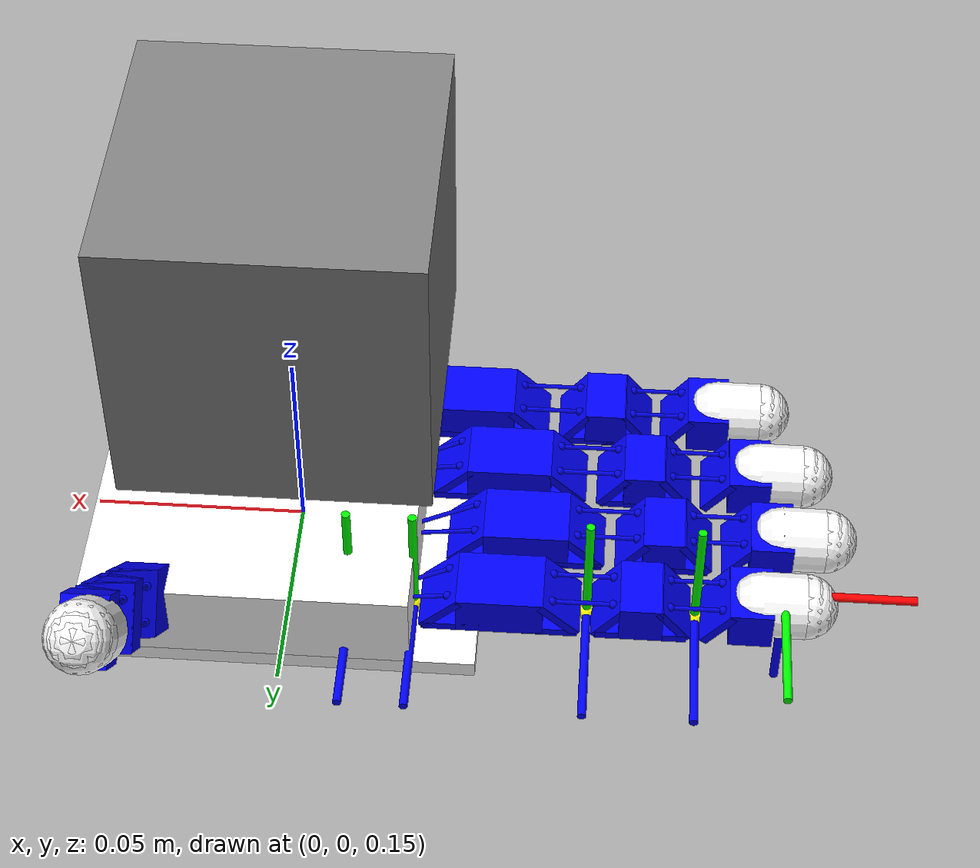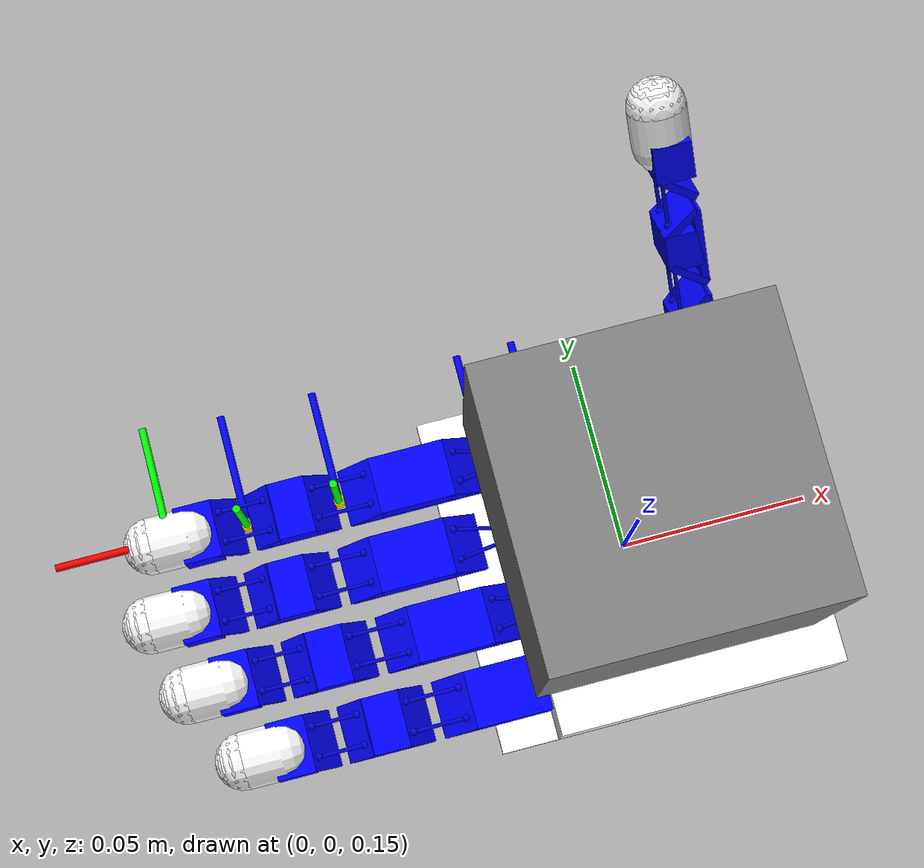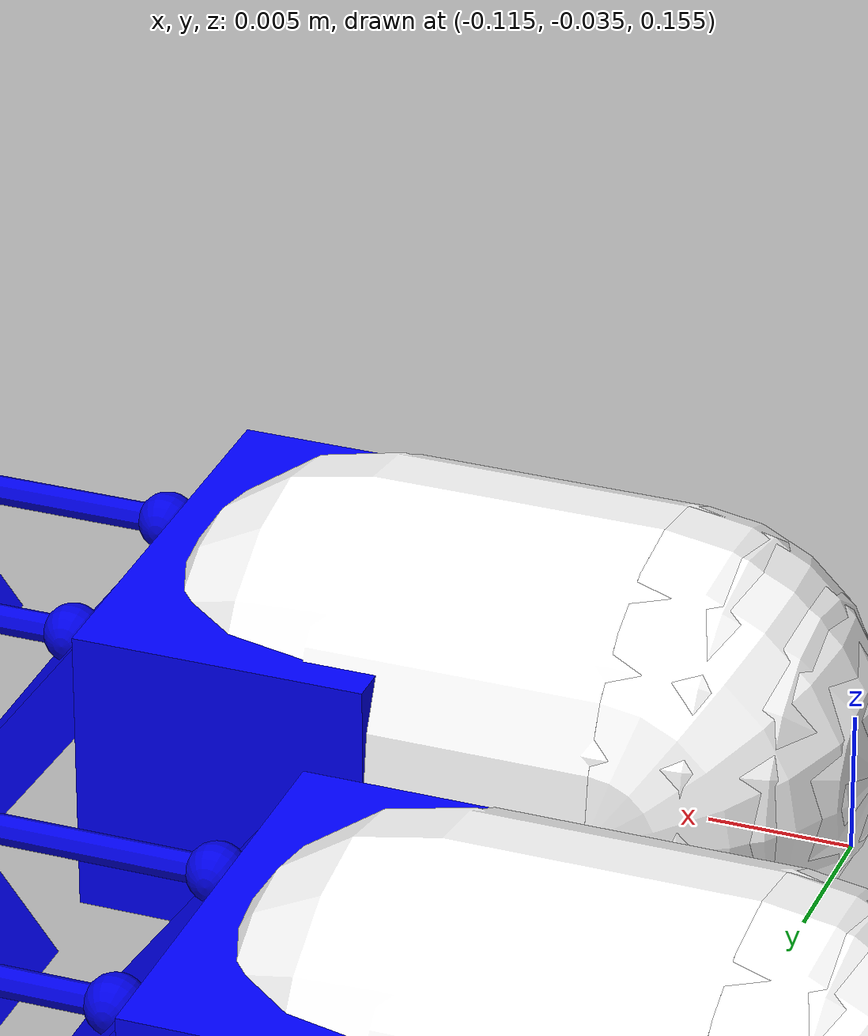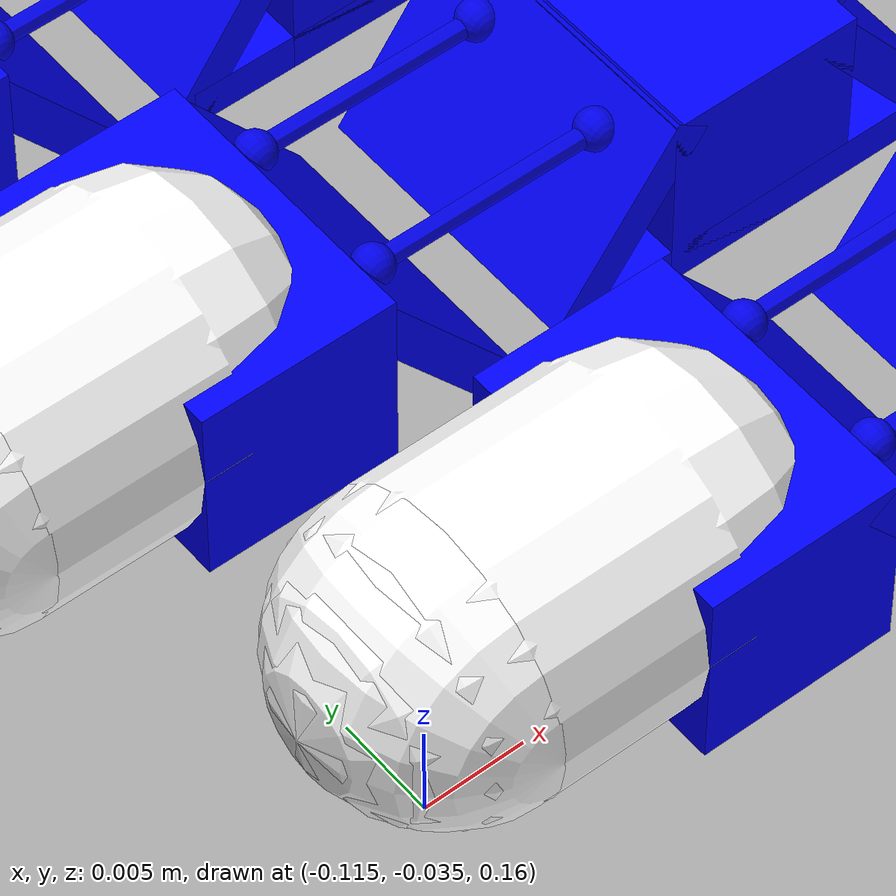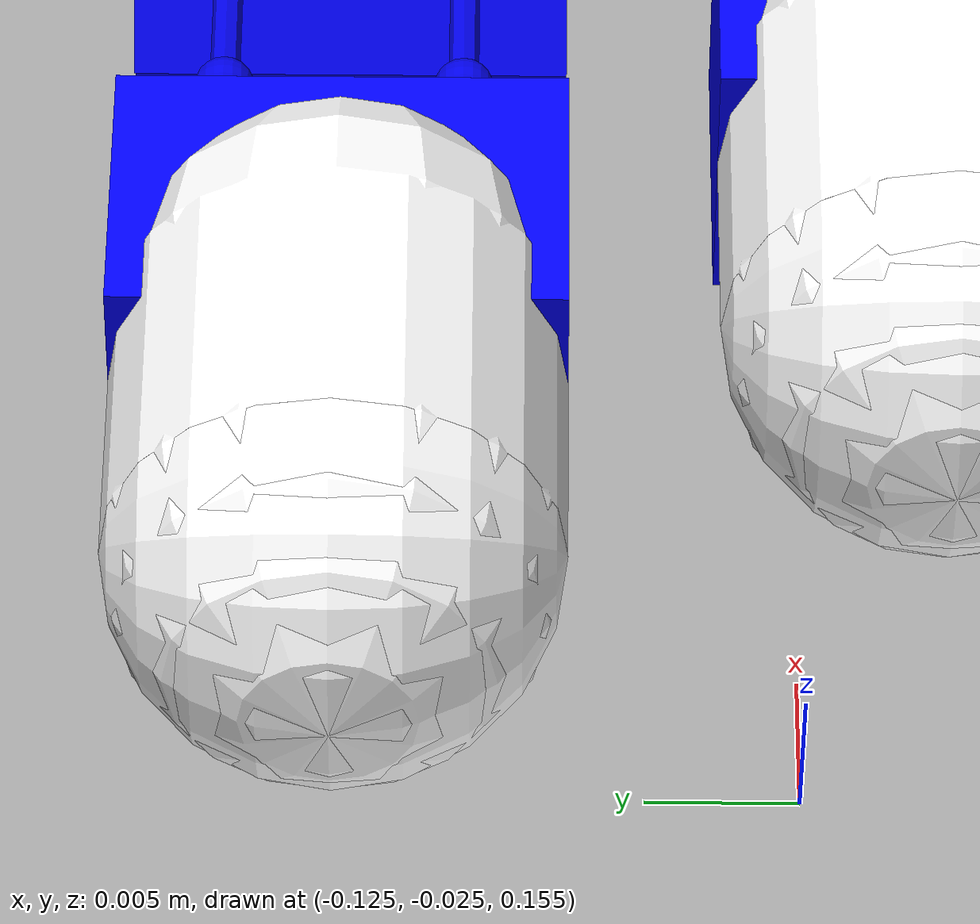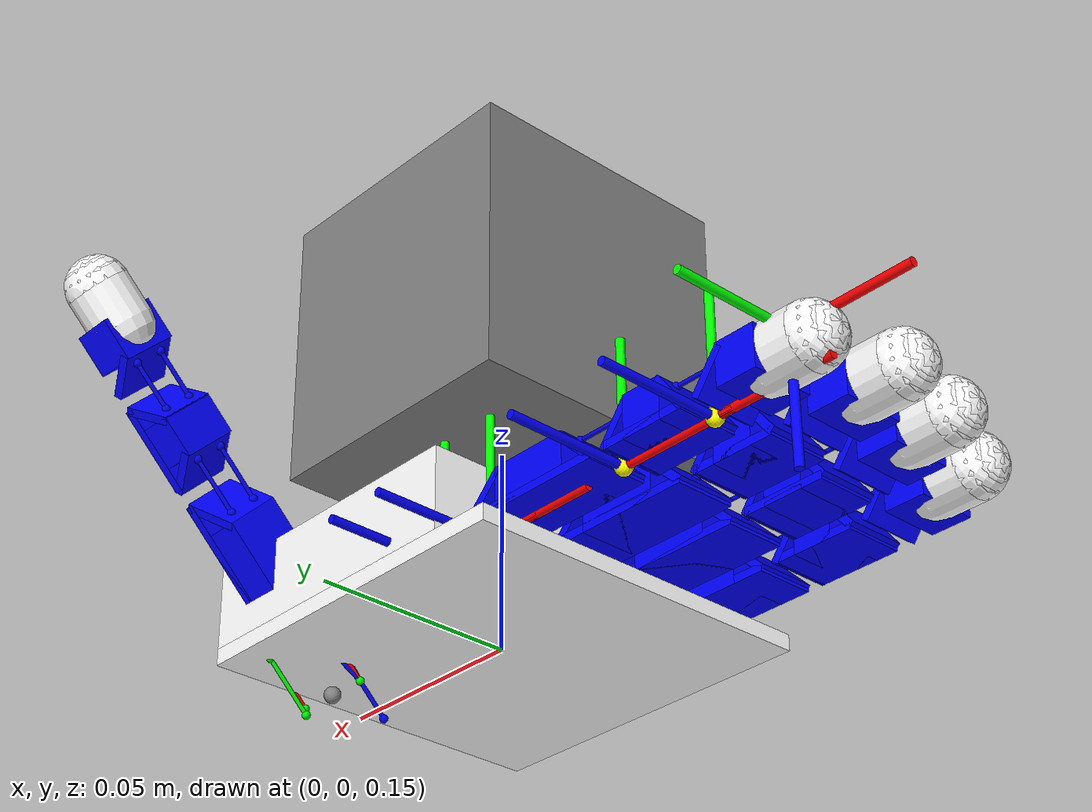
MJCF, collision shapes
<?xml version="1.0" ?>
<!-- Reorient手模型, 5x5 sphere tac sensors -->
<mujoco model="hand">
    <compiler angle="radian"/>
    <option integrator="implicitfast"/>
    <size njmax="5000" nconmax="10000"/>
    <!-- home state 存储了手的初始状态 -->
    <keyframe>
        <key name="home"
            qpos="0 0 0 0 0 0 0 0 0 0 0 0 0 0 0 0 0 0 0 0 0 0 0 0 0 0 0 0 0 0 0 0"
            qvel="0 0 0 0 0 0 0 0 0 0 0 0 0 0 0 0 0 0 0 0 0 0 0 0 0 0 0 0 0 0 0" />
    </keyframe>
    <option>
        <flag filterparent="disable"/>
    </option>
    <contact>
        <exclude body1="palm" body2="thumb_link_1"/>
        <exclude body1="palm" body2="index_link_1"/>
        <exclude body1="palm" body2="middle_link_1"/>
        <exclude body1="palm" body2="ring_link_1"/>
        <exclude body1="palm" body2="little_link_1"/>
    </contact>
    <asset>
        <mesh name="thumb_base_link" vertex="0.0 0.0 -0.0075 0.04 0.0 -0.0075 0.03 0.01 -0.0075 0.01 0.01 -0.0075 0.0 0.0 0.0075 0.04 0.0 0.0075 0.03 0.01 0.0075 0.01 0.01 0.0075" normal="-0.7734590803390136 -0.3203772410170408 -0.5469181606780271 0.7734590803390136 -0.3203772410170408 -0.5469181606780271 0.2971085791188998 0.7172835612062476 -0.6302624731310217 -0.2971085791188997 0.7172835612062475 -0.6302624731310217 -0.7734590803390136 -0.32037724101704074 0.5469181606780271 0.7734590803390138 -0.32037724101704057 0.5469181606780271 0.29710857911889976 0.7172835612062477 0.6302624731310216 -0.29710857911889976 0.7172835612062476 0.6302624731310217" face="1 0 3 3 2 1 7 4 5 5 6 7 5 4 1 1 4 0 6 5 2 2 5 1 4 7 0 0 7 3 7 6 3 3 6 2"/>
        <mesh name="thumb_link_1" vertex="0.0 0.0 -0.0075 0.04 0.0 -0.0075 0.03 0.01 -0.0075 0.01 0.01 -0.0075 0.0 0.0 0.0075 0.04 0.0 0.0075 0.03 0.01 0.0075 0.01 0.01 0.0075" normal="-0.7734590803390136 -0.3203772410170408 -0.5469181606780271 0.7734590803390136 -0.3203772410170408 -0.5469181606780271 0.2971085791188998 0.7172835612062476 -0.6302624731310217 -0.2971085791188997 0.7172835612062475 -0.6302624731310217 -0.7734590803390136 -0.32037724101704074 0.5469181606780271 0.7734590803390138 -0.32037724101704057 0.5469181606780271 0.29710857911889976 0.7172835612062477 0.6302624731310216 -0.29710857911889976 0.7172835612062476 0.6302624731310217" face="1 0 3 3 2 1 7 4 5 5 6 7 5 4 1 1 4 0 6 5 2 2 5 1 4 7 0 0 7 3 7 6 3 3 6 2"/>
        <mesh name="thumb_link_2" vertex="0.0 0.0 -0.0075 0.025 0.0 -0.0075 0.0175 0.01 -0.0075 0.007500000000000001 0.01 -0.0075 0.0 0.0 0.0075 0.025 0.0 0.0075 0.0175 0.01 0.0075 0.007500000000000001 0.01 0.0075" normal="-0.7464925414001442 -0.3732462707000721 -0.5508503490444955 0.7464925414001442 -0.3732462707000721 -0.5508503490444956 0.351257248032334 0.702514496064668 -0.618944043128098 -0.351257248032334 0.702514496064668 -0.618944043128098 -0.7464925414001442 -0.3732462707000721 0.5508503490444955 0.7464925414001442 -0.373246270700072 0.5508503490444956 0.351257248032334 0.7025144960646681 0.618944043128098 -0.351257248032334 0.702514496064668 0.618944043128098" face="1 0 3 3 2 1 7 4 5 5 6 7 5 4 1 1 4 0 6 5 2 2 5 1 4 7 0 0 7 3 7 6 3 3 6 2"/>
        <mesh name="thumb_link_3" vertex="0.0 0.0 -0.0075 0.025 0.0 -0.0075 0.0175 0.01 -0.0075 0.007500000000000001 0.01 -0.0075 0.0 0.0 0.0075 0.025 0.0 0.0075 0.0175 0.01 0.0075 0.007500000000000001 0.01 0.0075" normal="-0.7464925414001442 -0.3732462707000721 -0.5508503490444955 0.7464925414001442 -0.3732462707000721 -0.5508503490444956 0.351257248032334 0.702514496064668 -0.618944043128098 -0.351257248032334 0.702514496064668 -0.618944043128098 -0.7464925414001442 -0.3732462707000721 0.5508503490444955 0.7464925414001442 -0.373246270700072 0.5508503490444956 0.351257248032334 0.7025144960646681 0.618944043128098 -0.351257248032334 0.702514496064668 0.618944043128098" face="1 0 3 3 2 1 7 4 5 5 6 7 5 4 1 1 4 0 6 5 2 2 5 1 4 7 0 0 7 3 7 6 3 3 6 2"/>
        <mesh name="index_base_link" vertex="0.0 0.0 -0.0075 0.04 0.0 -0.0075 0.03 0.01 -0.0075 0.01 0.01 -0.0075 0.0 0.0 0.0075 0.04 0.0 0.0075 0.03 0.01 0.0075 0.01 0.01 0.0075" normal="-0.7734590803390136 -0.3203772410170408 -0.5469181606780271 0.7734590803390136 -0.3203772410170408 -0.5469181606780271 0.2971085791188998 0.7172835612062476 -0.6302624731310217 -0.2971085791188997 0.7172835612062475 -0.6302624731310217 -0.7734590803390136 -0.32037724101704074 0.5469181606780271 0.7734590803390138 -0.32037724101704057 0.5469181606780271 0.29710857911889976 0.7172835612062477 0.6302624731310216 -0.29710857911889976 0.7172835612062476 0.6302624731310217" face="1 0 3 3 2 1 7 4 5 5 6 7 5 4 1 1 4 0 6 5 2 2 5 1 4 7 0 0 7 3 7 6 3 3 6 2"/>
        <mesh name="index_link_1" vertex="0.0 0.0 -0.0075 0.04 0.0 -0.0075 0.03 0.01 -0.0075 0.01 0.01 -0.0075 0.0 0.0 0.0075 0.04 0.0 0.0075 0.03 0.01 0.0075 0.01 0.01 0.0075" normal="-0.7734590803390136 -0.3203772410170408 -0.5469181606780271 0.7734590803390136 -0.3203772410170408 -0.5469181606780271 0.2971085791188998 0.7172835612062476 -0.6302624731310217 -0.2971085791188997 0.7172835612062475 -0.6302624731310217 -0.7734590803390136 -0.32037724101704074 0.5469181606780271 0.7734590803390138 -0.32037724101704057 0.5469181606780271 0.29710857911889976 0.7172835612062477 0.6302624731310216 -0.29710857911889976 0.7172835612062476 0.6302624731310217" face="1 0 3 3 2 1 7 4 5 5 6 7 5 4 1 1 4 0 6 5 2 2 5 1 4 7 0 0 7 3 7 6 3 3 6 2"/>
        <mesh name="index_link_2" vertex="0.0 0.0 -0.0075 0.025 0.0 -0.0075 0.0175 0.01 -0.0075 0.007500000000000001 0.01 -0.0075 0.0 0.0 0.0075 0.025 0.0 0.0075 0.0175 0.01 0.0075 0.007500000000000001 0.01 0.0075" normal="-0.7464925414001442 -0.3732462707000721 -0.5508503490444955 0.7464925414001442 -0.3732462707000721 -0.5508503490444956 0.351257248032334 0.702514496064668 -0.618944043128098 -0.351257248032334 0.702514496064668 -0.618944043128098 -0.7464925414001442 -0.3732462707000721 0.5508503490444955 0.7464925414001442 -0.373246270700072 0.5508503490444956 0.351257248032334 0.7025144960646681 0.618944043128098 -0.351257248032334 0.702514496064668 0.618944043128098" face="1 0 3 3 2 1 7 4 5 5 6 7 5 4 1 1 4 0 6 5 2 2 5 1 4 7 0 0 7 3 7 6 3 3 6 2"/>
        <mesh name="index_link_3" vertex="0.0 0.0 -0.0075 0.025 0.0 -0.0075 0.0175 0.01 -0.0075 0.007500000000000001 0.01 -0.0075 0.0 0.0 0.0075 0.025 0.0 0.0075 0.0175 0.01 0.0075 0.007500000000000001 0.01 0.0075" normal="-0.7464925414001442 -0.3732462707000721 -0.5508503490444955 0.7464925414001442 -0.3732462707000721 -0.5508503490444956 0.351257248032334 0.702514496064668 -0.618944043128098 -0.351257248032334 0.702514496064668 -0.618944043128098 -0.7464925414001442 -0.3732462707000721 0.5508503490444955 0.7464925414001442 -0.373246270700072 0.5508503490444956 0.351257248032334 0.7025144960646681 0.618944043128098 -0.351257248032334 0.702514496064668 0.618944043128098" face="1 0 3 3 2 1 7 4 5 5 6 7 5 4 1 1 4 0 6 5 2 2 5 1 4 7 0 0 7 3 7 6 3 3 6 2"/>
        <mesh name="middle_base_link" vertex="0.0 0.0 -0.0075 0.04 0.0 -0.0075 0.03 0.01 -0.0075 0.01 0.01 -0.0075 0.0 0.0 0.0075 0.04 0.0 0.0075 0.03 0.01 0.0075 0.01 0.01 0.0075" normal="-0.7734590803390136 -0.3203772410170408 -0.5469181606780271 0.7734590803390136 -0.3203772410170408 -0.5469181606780271 0.2971085791188998 0.7172835612062476 -0.6302624731310217 -0.2971085791188997 0.7172835612062475 -0.6302624731310217 -0.7734590803390136 -0.32037724101704074 0.5469181606780271 0.7734590803390138 -0.32037724101704057 0.5469181606780271 0.29710857911889976 0.7172835612062477 0.6302624731310216 -0.29710857911889976 0.7172835612062476 0.6302624731310217" face="1 0 3 3 2 1 7 4 5 5 6 7 5 4 1 1 4 0 6 5 2 2 5 1 4 7 0 0 7 3 7 6 3 3 6 2"/>
        <mesh name="middle_link_1" vertex="0.0 0.0 -0.0075 0.04 0.0 -0.0075 0.03 0.01 -0.0075 0.01 0.01 -0.0075 0.0 0.0 0.0075 0.04 0.0 0.0075 0.03 0.01 0.0075 0.01 0.01 0.0075" normal="-0.7734590803390136 -0.3203772410170408 -0.5469181606780271 0.7734590803390136 -0.3203772410170408 -0.5469181606780271 0.2971085791188998 0.7172835612062476 -0.6302624731310217 -0.2971085791188997 0.7172835612062475 -0.6302624731310217 -0.7734590803390136 -0.32037724101704074 0.5469181606780271 0.7734590803390138 -0.32037724101704057 0.5469181606780271 0.29710857911889976 0.7172835612062477 0.6302624731310216 -0.29710857911889976 0.7172835612062476 0.6302624731310217" face="1 0 3 3 2 1 7 4 5 5 6 7 5 4 1 1 4 0 6 5 2 2 5 1 4 7 0 0 7 3 7 6 3 3 6 2"/>
        <mesh name="middle_link_2" vertex="0.0 0.0 -0.0075 0.025 0.0 -0.0075 0.0175 0.01 -0.0075 0.007500000000000001 0.01 -0.0075 0.0 0.0 0.0075 0.025 0.0 0.0075 0.0175 0.01 0.0075 0.007500000000000001 0.01 0.0075" normal="-0.7464925414001442 -0.3732462707000721 -0.5508503490444955 0.7464925414001442 -0.3732462707000721 -0.5508503490444956 0.351257248032334 0.702514496064668 -0.618944043128098 -0.351257248032334 0.702514496064668 -0.618944043128098 -0.7464925414001442 -0.3732462707000721 0.5508503490444955 0.7464925414001442 -0.373246270700072 0.5508503490444956 0.351257248032334 0.7025144960646681 0.618944043128098 -0.351257248032334 0.702514496064668 0.618944043128098" face="1 0 3 3 2 1 7 4 5 5 6 7 5 4 1 1 4 0 6 5 2 2 5 1 4 7 0 0 7 3 7 6 3 3 6 2"/>
        <mesh name="middle_link_3" vertex="0.0 0.0 -0.0075 0.025 0.0 -0.0075 0.0175 0.01 -0.0075 0.007500000000000001 0.01 -0.0075 0.0 0.0 0.0075 0.025 0.0 0.0075 0.0175 0.01 0.0075 0.007500000000000001 0.01 0.0075" normal="-0.7464925414001442 -0.3732462707000721 -0.5508503490444955 0.7464925414001442 -0.3732462707000721 -0.5508503490444956 0.351257248032334 0.702514496064668 -0.618944043128098 -0.351257248032334 0.702514496064668 -0.618944043128098 -0.7464925414001442 -0.3732462707000721 0.5508503490444955 0.7464925414001442 -0.373246270700072 0.5508503490444956 0.351257248032334 0.7025144960646681 0.618944043128098 -0.351257248032334 0.702514496064668 0.618944043128098" face="1 0 3 3 2 1 7 4 5 5 6 7 5 4 1 1 4 0 6 5 2 2 5 1 4 7 0 0 7 3 7 6 3 3 6 2"/>
        <mesh name="ring_base_link" vertex="0.0 0.0 -0.0075 0.04 0.0 -0.0075 0.03 0.01 -0.0075 0.01 0.01 -0.0075 0.0 0.0 0.0075 0.04 0.0 0.0075 0.03 0.01 0.0075 0.01 0.01 0.0075" normal="-0.7734590803390136 -0.3203772410170408 -0.5469181606780271 0.7734590803390136 -0.3203772410170408 -0.5469181606780271 0.2971085791188998 0.7172835612062476 -0.6302624731310217 -0.2971085791188997 0.7172835612062475 -0.6302624731310217 -0.7734590803390136 -0.32037724101704074 0.5469181606780271 0.7734590803390138 -0.32037724101704057 0.5469181606780271 0.29710857911889976 0.7172835612062477 0.6302624731310216 -0.29710857911889976 0.7172835612062476 0.6302624731310217" face="1 0 3 3 2 1 7 4 5 5 6 7 5 4 1 1 4 0 6 5 2 2 5 1 4 7 0 0 7 3 7 6 3 3 6 2"/>
        <mesh name="ring_link_1" vertex="0.0 0.0 -0.0075 0.04 0.0 -0.0075 0.03 0.01 -0.0075 0.01 0.01 -0.0075 0.0 0.0 0.0075 0.04 0.0 0.0075 0.03 0.01 0.0075 0.01 0.01 0.0075" normal="-0.7734590803390136 -0.3203772410170408 -0.5469181606780271 0.7734590803390136 -0.3203772410170408 -0.5469181606780271 0.2971085791188998 0.7172835612062476 -0.6302624731310217 -0.2971085791188997 0.7172835612062475 -0.6302624731310217 -0.7734590803390136 -0.32037724101704074 0.5469181606780271 0.7734590803390138 -0.32037724101704057 0.5469181606780271 0.29710857911889976 0.7172835612062477 0.6302624731310216 -0.29710857911889976 0.7172835612062476 0.6302624731310217" face="1 0 3 3 2 1 7 4 5 5 6 7 5 4 1 1 4 0 6 5 2 2 5 1 4 7 0 0 7 3 7 6 3 3 6 2"/>
        <mesh name="ring_link_2" vertex="0.0 0.0 -0.0075 0.025 0.0 -0.0075 0.0175 0.01 -0.0075 0.007500000000000001 0.01 -0.0075 0.0 0.0 0.0075 0.025 0.0 0.0075 0.0175 0.01 0.0075 0.007500000000000001 0.01 0.0075" normal="-0.7464925414001442 -0.3732462707000721 -0.5508503490444955 0.7464925414001442 -0.3732462707000721 -0.5508503490444956 0.351257248032334 0.702514496064668 -0.618944043128098 -0.351257248032334 0.702514496064668 -0.618944043128098 -0.7464925414001442 -0.3732462707000721 0.5508503490444955 0.7464925414001442 -0.373246270700072 0.5508503490444956 0.351257248032334 0.7025144960646681 0.618944043128098 -0.351257248032334 0.702514496064668 0.618944043128098" face="1 0 3 3 2 1 7 4 5 5 6 7 5 4 1 1 4 0 6 5 2 2 5 1 4 7 0 0 7 3 7 6 3 3 6 2"/>
        <mesh name="ring_link_3" vertex="0.0 0.0 -0.0075 0.025 0.0 -0.0075 0.0175 0.01 -0.0075 0.007500000000000001 0.01 -0.0075 0.0 0.0 0.0075 0.025 0.0 0.0075 0.0175 0.01 0.0075 0.007500000000000001 0.01 0.0075" normal="-0.7464925414001442 -0.3732462707000721 -0.5508503490444955 0.7464925414001442 -0.3732462707000721 -0.5508503490444956 0.351257248032334 0.702514496064668 -0.618944043128098 -0.351257248032334 0.702514496064668 -0.618944043128098 -0.7464925414001442 -0.3732462707000721 0.5508503490444955 0.7464925414001442 -0.373246270700072 0.5508503490444956 0.351257248032334 0.7025144960646681 0.618944043128098 -0.351257248032334 0.702514496064668 0.618944043128098" face="1 0 3 3 2 1 7 4 5 5 6 7 5 4 1 1 4 0 6 5 2 2 5 1 4 7 0 0 7 3 7 6 3 3 6 2"/>
        <mesh name="little_base_link" vertex="0.0 0.0 -0.0075 0.04 0.0 -0.0075 0.03 0.01 -0.0075 0.01 0.01 -0.0075 0.0 0.0 0.0075 0.04 0.0 0.0075 0.03 0.01 0.0075 0.01 0.01 0.0075" normal="-0.7734590803390136 -0.3203772410170408 -0.5469181606780271 0.7734590803390136 -0.3203772410170408 -0.5469181606780271 0.2971085791188998 0.7172835612062476 -0.6302624731310217 -0.2971085791188997 0.7172835612062475 -0.6302624731310217 -0.7734590803390136 -0.32037724101704074 0.5469181606780271 0.7734590803390138 -0.32037724101704057 0.5469181606780271 0.29710857911889976 0.7172835612062477 0.6302624731310216 -0.29710857911889976 0.7172835612062476 0.6302624731310217" face="1 0 3 3 2 1 7 4 5 5 6 7 5 4 1 1 4 0 6 5 2 2 5 1 4 7 0 0 7 3 7 6 3 3 6 2"/>
        <mesh name="little_link_1" vertex="0.0 0.0 -0.0075 0.04 0.0 -0.0075 0.03 0.01 -0.0075 0.01 0.01 -0.0075 0.0 0.0 0.0075 0.04 0.0 0.0075 0.03 0.01 0.0075 0.01 0.01 0.0075" normal="-0.7734590803390136 -0.3203772410170408 -0.5469181606780271 0.7734590803390136 -0.3203772410170408 -0.5469181606780271 0.2971085791188998 0.7172835612062476 -0.6302624731310217 -0.2971085791188997 0.7172835612062475 -0.6302624731310217 -0.7734590803390136 -0.32037724101704074 0.5469181606780271 0.7734590803390138 -0.32037724101704057 0.5469181606780271 0.29710857911889976 0.7172835612062477 0.6302624731310216 -0.29710857911889976 0.7172835612062476 0.6302624731310217" face="1 0 3 3 2 1 7 4 5 5 6 7 5 4 1 1 4 0 6 5 2 2 5 1 4 7 0 0 7 3 7 6 3 3 6 2"/>
        <mesh name="little_link_2" vertex="0.0 0.0 -0.0075 0.025 0.0 -0.0075 0.0175 0.01 -0.0075 0.007500000000000001 0.01 -0.0075 0.0 0.0 0.0075 0.025 0.0 0.0075 0.0175 0.01 0.0075 0.007500000000000001 0.01 0.0075" normal="-0.7464925414001442 -0.3732462707000721 -0.5508503490444955 0.7464925414001442 -0.3732462707000721 -0.5508503490444956 0.351257248032334 0.702514496064668 -0.618944043128098 -0.351257248032334 0.702514496064668 -0.618944043128098 -0.7464925414001442 -0.3732462707000721 0.5508503490444955 0.7464925414001442 -0.373246270700072 0.5508503490444956 0.351257248032334 0.7025144960646681 0.618944043128098 -0.351257248032334 0.702514496064668 0.618944043128098" face="1 0 3 3 2 1 7 4 5 5 6 7 5 4 1 1 4 0 6 5 2 2 5 1 4 7 0 0 7 3 7 6 3 3 6 2"/>
        <mesh name="little_link_3" vertex="0.0 0.0 -0.0075 0.025 0.0 -0.0075 0.0175 0.01 -0.0075 0.007500000000000001 0.01 -0.0075 0.0 0.0 0.0075 0.025 0.0 0.0075 0.0175 0.01 0.0075 0.007500000000000001 0.01 0.0075" normal="-0.7464925414001442 -0.3732462707000721 -0.5508503490444955 0.7464925414001442 -0.3732462707000721 -0.5508503490444956 0.351257248032334 0.702514496064668 -0.618944043128098 -0.351257248032334 0.702514496064668 -0.618944043128098 -0.7464925414001442 -0.3732462707000721 0.5508503490444955 0.7464925414001442 -0.373246270700072 0.5508503490444956 0.351257248032334 0.7025144960646681 0.618944043128098 -0.351257248032334 0.702514496064668 0.618944043128098" face="1 0 3 3 2 1 7 4 5 5 6 7 5 4 1 1 4 0 6 5 2 2 5 1 4 7 0 0 7 3 7 6 3 3 6 2"/>
    </asset>
    <option gravity="0 0 -9.81"/>
    <!-- 导入小道具 cube 的xml文件 -->
    <include file="./reorientation_cube.xml"/>
    <worldbody>
        <!-- 手的定义 -->
        <body name="palm" pos="0 0 0.15" euler="3.14 3.14 0">
            <joint name="palm_slide_x" type="slide" axis="1 0 0" range="-.5 .5" limited="true" solreflimit=".001 1" solimplimit="0.97 0.99 0.00001 0.1 2" damping="0.2"/>
            <joint name="palm_slide_y" type="slide" axis="0 1 0" range="-.5 .5" limited="true" solreflimit=".001 1" solimplimit="0.97 0.99 0.00001 0.1 2" damping="0.2"/>
            <joint name="palm_slide_z" type="slide" axis="0 0 1" range="-.2 .12" limited="true" solreflimit=".001 1" solimplimit="0.97 0.99 0.00001 0.1 2" damping="0.2"/>
            <joint name="palm_rotate_x" type="hinge" axis="1 0 0" range="-1.57 1.57" limited="true" solreflimit=".001 1" solimplimit="0.97 0.99 0.00001 0.1 2" damping="0.2"/>
            <joint name="palm_rotate_y" type="hinge" axis="0 1 0" range="-1.57 1.57" limited="true" solreflimit=".001 1" solimplimit="0.97 0.99 0.00001 0.1 2" damping="0.2"/>
            <joint name="palm_rotate_z" type="hinge" axis="0 0 1" range="-3.14 3.14" limited="true" solreflimit=".001 1" solimplimit="0.97 0.99 0.00001 0.1 2" damping="0.2"/>
            <geom type="box" size="0.045 0.045 0.002" rgba="1 1 1 1" density="200"/>
            <geom type="box" size="0.0375 0.045 0.01" pos="-0.0075 0 0.012" rgba="1 1 1 1" density="200"/>
            <body name="thumb_base_link" pos="-0.035 -0.02 -0.005" euler="-0.785 0.0 -1.57">
                <geom conaffinity="0" contype="0" type="sphere" size=".002"/>
                <site name="thumb_ty_1_1" pos="0 0 0.01" size="0.001" rgba="0 0.9 0 1"/>
                <site name="thumb_ty_2_1" pos="0 0 -0.01" size="0.001" rgba="0 0.9 0 1"/>
                <site name="thumb_tx_1_1" pos="0 0.01 0" size="0.001" rgba="0 0.9 0 1"/>
                <site name="thumb_tx_2_1" pos="0 -0.01 0" size="0.001" rgba="0 0.9 0 1"/>
                <site name="thumb_t12" pos="0 0.01 0" size="0.001" rgba="0 0 0.9 1"/>
                <site name="thumb_t0" pos="-0.01 0.01 0" size="0.001" rgba="0 0 0.9 1"/>
                <body name="thumb_link_1" pos="0.015 0 0">
                    <joint name="thumb_universal_1" pos="0 0 0" axis="0 0 1" damping="0.1"/>
                    <joint name="thumb_universal_2" pos="0 0 0" axis="0 1 0" damping="0.1"/>
                    <geom type="box" pos="0.02 0.005 0" size="0.01 0.005 0.0075" name="thumb_link_1_box_center" density="200" friction="0.7 0.05 0.0002" solref="0.02 1.5" solimp="0.9 0.99 0.001" rgba="0 0 1 0"/>
                    <geom type="box" pos="0.03358578654972743 0.004999436911938167 0" size="0.0060674574081405145 0.001 0.0075" euler="0 0 -0.785" name="thumb_link_1_box_slope1" density="200" friction="0.7 0.05 0.0002" solref="0.02 1.5" solimp="0.9 0.99 0.001" rgba="0 0 1 0"/>
                    <geom type="box" pos="0.006414213450272566 0.005000563088061833 0" size="0.0060674574081405145 0.001 0.0075" euler="0 0 0.785" name="thumb_link_1_box_slope2" density="200" friction="0.7 0.05 0.0002" solref="0.02 1.5" solimp="0.9 0.99 0.001" rgba="0 0 1 0"/>
                    <geom type="box" pos="0.02 0.001 0" size="0.018000000000000002 0.001 0.0075" euler="0 0 0" name="thumb_link_1_box_bottom" density="200" friction="0.7 0.05 0.0002" solref="0.02 1.5" solimp="0.9 0.99 0.001" rgba="0 0 1 0"/>
                    <geom conaffinity="0" contype="0" type="mesh" rgba="1 1 1 1" mesh="thumb_link_1"/>
                    <site name="thumb_ty_1_2" pos="0 0 0.01" size="0.001" rgba="0 0.9 0 1"/>
                    <site name="thumb_ty_2_2" pos="0 0 -0.01" size="0.001" rgba="0 0.9 0 1"/>
                    <site name="thumb_tx_1_2" pos="0 0.01 0" size="0.001" rgba="0 0.9 0 1"/>
                    <site name="thumb_tx_2_2" pos="0 -0.01 0" size="0.001" rgba="0 0.9 0 1"/>
                    <site name="thumb_t1_1_1" pos="0.008 0.008 0.004" size="0.001" rgba="0 0 0.9 1"/>
                    <site name="thumb_t2_1_1" pos="0.008 0.008 -0.004" size="0.001" rgba="0 0 0.9 1"/>
                    <site name="thumb_t1_1_2" pos="0.032 0.008 0.004" size="0.001" rgba="0 0 0.9 1"/>
                    <site name="thumb_t2_1_2" pos="0.032 0.008 -0.004" size="0.001" rgba="0 0 0.9 1"/>
                    <body name="thumb_link_2" pos="0.04 0 0">
                        <joint name="thumb_joint_1" pos="0 0 0" axis="0 0 1" stiffness="0.1" springref="0.0" damping="0.2" range="0 3.14"/>
                        <geom type="box" pos="0.0125 0.005 0" size="0.005 0.005 0.0075" name="thumb_link_2_box_center" density="200" friction="0.7 0.05 0.0002" solref="0.02 1.5" solimp="0.9 0.99 0.001" rgba="0 0 1 0"/>
                        <geom type="box" pos="0.019849544644419077 0.005196786170816701 0" size="0.005477355448802637 0.001 0.0075" euler="0 0 -0.925" name="thumb_link_2_box_slope1" density="200" friction="0.7 0.05 0.0002" solref="0.02 1.5" solimp="0.9 0.99 0.001" rgba="0 0 1 0"/>
                        <geom type="box" pos="0.0051504553555809275 0.004803213829183299 0" size="0.005477355448802637 0.001 0.0075" euler="0 0 0.925" name="thumb_link_2_box_slope2" density="200" friction="0.7 0.05 0.0002" solref="0.02 1.5" solimp="0.9 0.99 0.001" rgba="0 0 1 0"/>
                        <geom type="box" pos="0.0125 0.001 0" size="0.0105 0.001 0.0075" euler="0 0 0" name="thumb_link_2_box_bottom" density="200" friction="0.7 0.05 0.0002" solref="0.02 1.5" solimp="0.9 0.99 0.001" rgba="0 0 1 0"/>
                        <geom conaffinity="0" contype="0" type="mesh" rgba="1 1 1 1" mesh="thumb_link_2"/>
                        <site name="thumb_t1_2_1" pos="0.006 0.008 0.004" size="0.001" rgba="0 0 0.9 1"/>
                        <site name="thumb_t2_2_1" pos="0.006 0.008 -0.004" size="0.001" rgba="0 0 0.9 1"/>
                        <site name="thumb_t1_2_2" pos="0.019000000000000003 0.008 0.004" size="0.001" rgba="0 0 0.9 1"/>
                        <site name="thumb_t2_2_2" pos="0.019000000000000003 0.008 -0.004" size="0.001" rgba="0 0 0.9 1"/>
                        <body name="thumb_link_3" pos="0.025 0 0">
                            <joint name="thumb_joint_2" pos="0 0 0" axis="0 0 1" stiffness="0.1" springref="0.0" damping="0.2" range="0 3.14"/>
                            <geom type="box" pos="0.0125 0.005 0" size="0.005 0.005 0.0075" name="thumb_link_3_box_center" density="200" friction="0.7 0.05 0.0002" solref="0.02 1.5" solimp="0.9 0.99 0.001" rgba="0 0 1 0"/>
                            <geom type="box" pos="0.0051504553555809275 0.004803213829183299 0" size="0.005477355448802637 0.001 0.0075" euler="0 0 0.925" name="thumb_link_3_box_slope2" density="200" friction="0.7 0.05 0.0002" solref="0.02 1.5" solimp="0.9 0.99 0.001" rgba="0 0 1 0"/>
                            <geom type="sphere" pos="0.025 0.006 0" size="0.0075" rgba="1 1 1 .3" density="200" friction="0.7 0.05 0.0002" solref="0.02 1.5" solimp="0.9 0.99 0.001"/>
                            <geom type="capsule" euler="0 1.57 0" pos="0.02 0.006 0" size="0.0075 0.005000000000000001" rgba="1 1 1 .3" density="200" friction="0.7 0.05 0.0002" solref="0.02 1.5" solimp="0.9 0.99 0.001"/>
                            <geom conaffinity="0" contype="0" type="mesh" rgba="1 1 1 1" mesh="thumb_link_3"/>
                            <site name="thumb_t1_3" pos="0.006 0.008 0.004" size="0.001" rgba="0 0 0.9 1"/>
                            <site name="thumb_t2_3" pos="0.006 0.008 -0.004" size="0.001" rgba="0 0 0.9 1"/>
                            <body name="thumb_fingertip" pos="0.02 0.01 0" euler="1.57 0 0">
                                <geom conaffinity="0" contype="0" type="sphere" pos="0 0 0" size=".001" rgba=".9 0 0 .1"/>
                                <body name="thumb_markerB_0_0" pos="-0.003 -0.003 -0.002">
                                    <geom name="thumb_markerG_0_0" type="sphere" conaffinity="1" contype="1" rgba=".9 0 0 .9" size="0.0003" mass=".0001" friction="0.7 0.05 0.0002" solref="0.02 1.5" solimp="0.9 0.99 0.001" condim="3"/>
                                </body>
                                <body name="thumb_markerB_0_1" pos="-0.003 -0.0015 -0.002">
                                    <geom name="thumb_markerG_0_1" type="sphere" conaffinity="1" contype="1" rgba=".9 0 0 .9" size="0.0003" mass=".0001" friction="0.7 0.05 0.0002" solref="0.02 1.5" solimp="0.9 0.99 0.001" condim="3"/>
                                </body>
                                <body name="thumb_markerB_0_2" pos="-0.003 0.0 -0.002">
                                    <geom name="thumb_markerG_0_2" type="sphere" conaffinity="1" contype="1" rgba=".9 0 0 .9" size="0.0003" mass=".0001" friction="0.7 0.05 0.0002" solref="0.02 1.5" solimp="0.9 0.99 0.001" condim="3"/>
                                </body>
                                <body name="thumb_markerB_0_3" pos="-0.003 0.0015000000000000005 -0.002">
                                    <geom name="thumb_markerG_0_3" type="sphere" conaffinity="1" contype="1" rgba=".9 0 0 .9" size="0.0003" mass=".0001" friction="0.7 0.05 0.0002" solref="0.02 1.5" solimp="0.9 0.99 0.001" condim="3"/>
                                </body>
                                <body name="thumb_markerB_0_4" pos="-0.003 0.003 -0.002">
                                    <geom name="thumb_markerG_0_4" type="sphere" conaffinity="1" contype="1" rgba=".9 0 0 .9" size="0.0003" mass=".0001" friction="0.7 0.05 0.0002" solref="0.02 1.5" solimp="0.9 0.99 0.001" condim="3"/>
                                </body>
                                <body name="thumb_markerB_1_0" pos="-0.0015 -0.003 -0.002">
                                    <geom name="thumb_markerG_1_0" type="sphere" conaffinity="1" contype="1" rgba=".9 0 0 .9" size="0.0003" mass=".0001" friction="0.7 0.05 0.0002" solref="0.02 1.5" solimp="0.9 0.99 0.001" condim="3"/>
                                </body>
                                <body name="thumb_markerB_1_1" pos="-0.0015 -0.0015 -0.002">
                                    <geom name="thumb_markerG_1_1" type="sphere" conaffinity="1" contype="1" rgba=".9 0 0 .9" size="0.0003" mass=".0001" friction="0.7 0.05 0.0002" solref="0.02 1.5" solimp="0.9 0.99 0.001" condim="3"/>
                                </body>
                                <body name="thumb_markerB_1_2" pos="-0.0015 0.0 -0.002">
                                    <geom name="thumb_markerG_1_2" type="sphere" conaffinity="1" contype="1" rgba=".9 0 0 .9" size="0.0003" mass=".0001" friction="0.7 0.05 0.0002" solref="0.02 1.5" solimp="0.9 0.99 0.001" condim="3"/>
                                </body>
                                <body name="thumb_markerB_1_3" pos="-0.0015 0.0015000000000000005 -0.002">
                                    <geom name="thumb_markerG_1_3" type="sphere" conaffinity="1" contype="1" rgba=".9 0 0 .9" size="0.0003" mass=".0001" friction="0.7 0.05 0.0002" solref="0.02 1.5" solimp="0.9 0.99 0.001" condim="3"/>
                                </body>
                                <body name="thumb_markerB_1_4" pos="-0.0015 0.003 -0.002">
                                    <geom name="thumb_markerG_1_4" type="sphere" conaffinity="1" contype="1" rgba=".9 0 0 .9" size="0.0003" mass=".0001" friction="0.7 0.05 0.0002" solref="0.02 1.5" solimp="0.9 0.99 0.001" condim="3"/>
                                </body>
                                <body name="thumb_markerB_2_0" pos="0.0 -0.003 -0.002">
                                    <geom name="thumb_markerG_2_0" type="sphere" conaffinity="1" contype="1" rgba=".9 0 0 .9" size="0.0003" mass=".0001" friction="0.7 0.05 0.0002" solref="0.02 1.5" solimp="0.9 0.99 0.001" condim="3"/>
                                </body>
                                <body name="thumb_markerB_2_1" pos="0.0 -0.0015 -0.002">
                                    <geom name="thumb_markerG_2_1" type="sphere" conaffinity="1" contype="1" rgba=".9 0 0 .9" size="0.0003" mass=".0001" friction="0.7 0.05 0.0002" solref="0.02 1.5" solimp="0.9 0.99 0.001" condim="3"/>
                                </body>
                                <body name="thumb_markerB_2_2" pos="0.0 0.0 -0.002">
                                    <geom name="thumb_markerG_2_2" type="sphere" conaffinity="1" contype="1" rgba=".9 0 0 .9" size="0.0003" mass=".0001" friction="0.7 0.05 0.0002" solref="0.02 1.5" solimp="0.9 0.99 0.001" condim="3"/>
                                </body>
                                <body name="thumb_markerB_2_3" pos="0.0 0.0015000000000000005 -0.002">
                                    <geom name="thumb_markerG_2_3" type="sphere" conaffinity="1" contype="1" rgba=".9 0 0 .9" size="0.0003" mass=".0001" friction="0.7 0.05 0.0002" solref="0.02 1.5" solimp="0.9 0.99 0.001" condim="3"/>
                                </body>
                                <body name="thumb_markerB_2_4" pos="0.0 0.003 -0.002">
                                    <geom name="thumb_markerG_2_4" type="sphere" conaffinity="1" contype="1" rgba=".9 0 0 .9" size="0.0003" mass=".0001" friction="0.7 0.05 0.0002" solref="0.02 1.5" solimp="0.9 0.99 0.001" condim="3"/>
                                </body>
                                <body name="thumb_markerB_3_0" pos="0.0015000000000000005 -0.003 -0.002">
                                    <geom name="thumb_markerG_3_0" type="sphere" conaffinity="1" contype="1" rgba=".9 0 0 .9" size="0.0003" mass=".0001" friction="0.7 0.05 0.0002" solref="0.02 1.5" solimp="0.9 0.99 0.001" condim="3"/>
                                </body>
                                <body name="thumb_markerB_3_1" pos="0.0015000000000000005 -0.0015 -0.002">
                                    <geom name="thumb_markerG_3_1" type="sphere" conaffinity="1" contype="1" rgba=".9 0 0 .9" size="0.0003" mass=".0001" friction="0.7 0.05 0.0002" solref="0.02 1.5" solimp="0.9 0.99 0.001" condim="3"/>
                                </body>
                                <body name="thumb_markerB_3_2" pos="0.0015000000000000005 0.0 -0.002">
                                    <geom name="thumb_markerG_3_2" type="sphere" conaffinity="1" contype="1" rgba=".9 0 0 .9" size="0.0003" mass=".0001" friction="0.7 0.05 0.0002" solref="0.02 1.5" solimp="0.9 0.99 0.001" condim="3"/>
                                </body>
                                <body name="thumb_markerB_3_3" pos="0.0015000000000000005 0.0015000000000000005 -0.002">
                                    <geom name="thumb_markerG_3_3" type="sphere" conaffinity="1" contype="1" rgba=".9 0 0 .9" size="0.0003" mass=".0001" friction="0.7 0.05 0.0002" solref="0.02 1.5" solimp="0.9 0.99 0.001" condim="3"/>
                                </body>
                                <body name="thumb_markerB_3_4" pos="0.0015000000000000005 0.003 -0.002">
                                    <geom name="thumb_markerG_3_4" type="sphere" conaffinity="1" contype="1" rgba=".9 0 0 .9" size="0.0003" mass=".0001" friction="0.7 0.05 0.0002" solref="0.02 1.5" solimp="0.9 0.99 0.001" condim="3"/>
                                </body>
                                <body name="thumb_markerB_4_0" pos="0.003 -0.003 -0.002">
                                    <geom name="thumb_markerG_4_0" type="sphere" conaffinity="1" contype="1" rgba=".9 0 0 .9" size="0.0003" mass=".0001" friction="0.7 0.05 0.0002" solref="0.02 1.5" solimp="0.9 0.99 0.001" condim="3"/>
                                </body>
                                <body name="thumb_markerB_4_1" pos="0.003 -0.0015 -0.002">
                                    <geom name="thumb_markerG_4_1" type="sphere" conaffinity="1" contype="1" rgba=".9 0 0 .9" size="0.0003" mass=".0001" friction="0.7 0.05 0.0002" solref="0.02 1.5" solimp="0.9 0.99 0.001" condim="3"/>
                                </body>
                                <body name="thumb_markerB_4_2" pos="0.003 0.0 -0.002">
                                    <geom name="thumb_markerG_4_2" type="sphere" conaffinity="1" contype="1" rgba=".9 0 0 .9" size="0.0003" mass=".0001" friction="0.7 0.05 0.0002" solref="0.02 1.5" solimp="0.9 0.99 0.001" condim="3"/>
                                </body>
                                <body name="thumb_markerB_4_3" pos="0.003 0.0015000000000000005 -0.002">
                                    <geom name="thumb_markerG_4_3" type="sphere" conaffinity="1" contype="1" rgba=".9 0 0 .9" size="0.0003" mass=".0001" friction="0.7 0.05 0.0002" solref="0.02 1.5" solimp="0.9 0.99 0.001" condim="3"/>
                                </body>
                                <body name="thumb_markerB_4_4" pos="0.003 0.003 -0.002">
                                    <geom name="thumb_markerG_4_4" type="sphere" conaffinity="1" contype="1" rgba=".9 0 0 .9" size="0.0003" mass=".0001" friction="0.7 0.05 0.0002" solref="0.02 1.5" solimp="0.9 0.99 0.001" condim="3"/>
                                </body>
                            </body>
                        </body>
                    </body>
                </body>
            </body>
            <body name="index_base_link" pos="0.015 -0.03 0.005" euler="1.57 0.0 0.0">
                <!-- visable xyz frames -->
                <site name="index_base_link_frame_origin" type="sphere" size="0.002" rgba="1 1 0 1" pos="0 0 0"/>
                <geom name="index_base_link_X" type="cylinder" size="0.001" fromto="0 0 0 0.03 0 0" rgba="1 0 0 1" contype="0" conaffinity="0"/>
                <geom name="index_base_link_Y" type="cylinder" size="0.001" fromto="0 0 0 0 0.03 0" rgba="0 1 0 1" contype="0" conaffinity="0"/>
                <geom name="index_base_link_Z" type="cylinder" size="0.001" fromto="0 0 0 0 0 0.03" rgba="0 0 1 1" contype="0" conaffinity="0"/>
                <joint name="index_swing" axis="0 -1 0" range="0 0.5" damping="0.2"/>
                <geom conaffinity="0" contype="0" type="sphere" size=".002"/>
                <site name="index_t12" pos="0 0 0" size="0.001" rgba="0 0 0.9 1"/>
                <site name="index_t0" pos="-0.01 0 0" size="0.001" rgba="0 0 0.9 1"/>
                <body name="index_link_1" pos="0.015 0 0">
                    <!-- visable xyz frames -->
                    <site name="index_link_1_frame_origin" type="sphere" size="0.002" rgba="1 1 0 1" pos="0 0 0"/>
                    <geom name="index_link1_X" type="cylinder" size="0.001" fromto="0 0 0 0.03 0 0" rgba="1 0 0 1" contype="0" conaffinity="0"/>
                    <geom name="index_link1_Y" type="cylinder" size="0.001" fromto="0 0 0 0 0.03 0" rgba="0 1 0 1" contype="0" conaffinity="0"/>
                    <geom name="index_link1_Z" type="cylinder" size="0.001" fromto="0 0 0 0 0 0.03" rgba="0 0 1 1" contype="0" conaffinity="0"/>
                    <joint name="index_joint_0" pos="0 0 0" axis="0 0 1" stiffness="0.2" springref="0.0" damping="0.2" range="0 3.14" frictionloss="0.08"/>
                    <geom type="box" pos="0.02 0.005 0" size="0.01 0.005 0.0075" name="index_link_1_box_center" density="200" friction="0.7 0.05 0.0002" solref="0.02 1.5" solimp="0.9 0.99 0.001" rgba="0 0 1 0"/>
                    <geom type="box" pos="0.03358578654972743 0.004999436911938167 0" size="0.0060674574081405145 0.001 0.0075" euler="0 0 -0.785" name="index_link_1_box_slope1" density="200" friction="0.7 0.05 0.0002" solref="0.02 1.5" solimp="0.9 0.99 0.001" rgba="0 0 1 0"/>
                    <geom type="box" pos="0.006414213450272566 0.005000563088061833 0" size="0.0060674574081405145 0.001 0.0075" euler="0 0 0.785" name="index_link_1_box_slope2" density="200" friction="0.7 0.05 0.0002" solref="0.02 1.5" solimp="0.9 0.99 0.001" rgba="0 0 1 0"/>
                    <geom type="box" pos="0.02 0.001 0" size="0.018000000000000002 0.001 0.0075" euler="0 0 0" name="index_link_1_box_bottom" density="200" friction="0.7 0.05 0.0002" solref="0.02 1.5" solimp="0.9 0.99 0.001" rgba="0 0 1 0"/>
                    <geom conaffinity="0" contype="0" type="mesh" rgba="1 1 1 1" mesh="index_link_1"/>
                    <site name="index_t1_1_1" pos="0.008 0.008 0.004" size="0.001" rgba="0 0 0.9 1"/>
                    <site name="index_t2_1_1" pos="0.008 0.008 -0.004" size="0.001" rgba="0 0 0.9 1"/>
                    <site name="index_t1_1_2" pos="0.032 0.008 0.004" size="0.001" rgba="0 0 0.9 1"/>
                    <site name="index_t2_1_2" pos="0.032 0.008 -0.004" size="0.001" rgba="0 0 0.9 1"/>
                    <body name="index_link_2" pos="0.04 0 0">
                        <!-- visable xyz frames -->
                        <site name="index_link_2_frame_origin" type="sphere" size="0.002" rgba="1 1 0 1" pos="0 0 0"/>
                        <geom name="index_link2_X" type="cylinder" size="0.001" fromto="0 0 0 0.03 0 0" rgba="1 0 0 1" contype="0" conaffinity="0"/>
                        <geom name="index_link2_Y" type="cylinder" size="0.001" fromto="0 0 0 0 0.03 0" rgba="0 1 0 1" contype="0" conaffinity="0"/>
                        <geom name="index_link2_Z" type="cylinder" size="0.001" fromto="0 0 0 0 0 0.03" rgba="0 0 1 1" contype="0" conaffinity="0"/>`
                        <joint name="index_joint_1" pos="0 0 0" axis="0 0 1" stiffness="0.2" springref="0.0" damping="0.05" range="0 3.14" frictionloss="0.04"/>
                        <geom type="box" pos="0.0125 0.005 0" size="0.005 0.005 0.0075" name="index_link_2_box_center" density="200" friction="0.7 0.05 0.0002" solref="0.02 1.5" solimp="0.9 0.99 0.001" rgba="0 0 1 0"/>
                        <geom type="box" pos="0.019849544644419077 0.005196786170816701 0" size="0.005477355448802637 0.001 0.0075" euler="0 0 -0.925" name="index_link_2_box_slope1" density="200" friction="0.7 0.05 0.0002" solref="0.02 1.5" solimp="0.9 0.99 0.001" rgba="0 0 1 0"/>
                        <geom type="box" pos="0.0051504553555809275 0.004803213829183299 0" size="0.005477355448802637 0.001 0.0075" euler="0 0 0.925" name="index_link_2_box_slope2" density="200" friction="0.7 0.05 0.0002" solref="0.02 1.5" solimp="0.9 0.99 0.001" rgba="0 0 1 0"/>
                        <geom type="box" pos="0.0125 0.001 0" size="0.0105 0.001 0.0075" euler="0 0 0" name="index_link_2_box_bottom" density="200" friction="0.7 0.05 0.0002" solref="0.02 1.5" solimp="0.9 0.99 0.001" rgba="0 0 1 0"/>
                        <geom conaffinity="0" contype="0" type="mesh" rgba="1 1 1 1" mesh="index_link_2"/>
                        <site name="index_t1_2_1" pos="0.006 0.008 0.004" size="0.001" rgba="0 0 0.9 1"/>
                        <site name="index_t2_2_1" pos="0.006 0.008 -0.004" size="0.001" rgba="0 0 0.9 1"/>
                        <site name="index_t1_2_2" pos="0.019000000000000003 0.008 0.004" size="0.001" rgba="0 0 0.9 1"/>
                        <site name="index_t2_2_2" pos="0.019000000000000003 0.008 -0.004" size="0.001" rgba="0 0 0.9 1"/>
                        <body name="index_link_3" pos="0.025 0 0">
                            <!-- visable xyz frames -->
                            <site name="index_link_3_frame_origin" type="sphere" size="0.002" rgba="1 1 0 1" pos="0 0 0"/>
                            <geom name="index_link3_X" type="cylinder" size="0.001" fromto="0 0 0 0.03 0 0" rgba="1 0 0 1" contype="0" conaffinity="0"/>
                            <geom name="index_link3_Y" type="cylinder" size="0.001" fromto="0 0 0 0 0.03 0" rgba="0 1 0 1" contype="0" conaffinity="0"/>
                            <geom name="index_link3_Z" type="cylinder" size="0.001" fromto="0 0 0 0 0 0.03" rgba="0 0 1 1" contype="0" conaffinity="0"/>
                            <joint name="index_joint_2" pos="0 0 0" axis="0 0 1" stiffness="0.2" springref="0.0" damping="0.01" range="0 1.3" frictionloss="0.02"/>
                            <geom type="box" pos="0.0125 0.005 0" size="0.005 0.005 0.0075" name="index_link_3_box_center" density="200" friction="0.7 0.05 0.0002" solref="0.02 1.5" solimp="0.9 0.99 0.001" rgba="0 0 1 0"/>
                            <geom type="box" pos="0.0051504553555809275 0.004803213829183299 0" size="0.005477355448802637 0.001 0.0075" euler="0 0 0.925" name="index_link_3_box_slope2" density="200" friction="0.7 0.05 0.0002" solref="0.02 1.5" solimp="0.9 0.99 0.001" rgba="0 0 1 0"/>
                            <geom type="sphere" pos="0.025 0.006 0" size="0.0075" rgba="1 1 1 .3" density="200" friction="0.7 0.05 0.0002" solref="0.02 1.5" solimp="0.9 0.99 0.001"/>
                            <geom type="capsule" euler="0 1.57 0" pos="0.02 0.006 0" size="0.0075 0.005000000000000001" rgba="1 1 1 .3" density="200" friction="0.7 0.05 0.0002" solref="0.02 1.5" solimp="0.9 0.99 0.001"/>
                            <geom conaffinity="0" contype="0" type="mesh" rgba="1 1 1 1" mesh="index_link_3"/>
                            <site name="index_t1_3" pos="0.006 0.008 0.004" size="0.001" rgba="0 0 0.9 1"/>
                            <site name="index_t2_3" pos="0.006 0.008 -0.004" size="0.001" rgba="0 0 0.9 1"/>
                            <body name="index_fingertip" pos="0.02 0.01 0" euler="1.57 0 0">
                                <!-- visable xyz frames -->
                                <site name="index_tip_frame_origin" type="sphere" size="0.002" rgba="1 1 0 1" pos="0 0 0"/>
                                <geom name="index_tip_X" type="cylinder" size="0.001" fromto="0 0 0 0.03 0 0" rgba="1 0 0 1" contype="0" conaffinity="0"/>
                                <geom name="index_tip_Y" type="cylinder" size="0.001" fromto="0 0 0 0 0.03 0" rgba="0 1 0 1" contype="0" conaffinity="0"/>
                                <geom name="index_tip_Z" type="cylinder" size="0.001" fromto="0 0 0 0 0 0.03" rgba="0 0 1 1" contype="0" conaffinity="0"/>
                                <geom conaffinity="0" contype="0" type="sphere" pos="0 0 0" size=".001" rgba=".9 0 0 .1"/>
                                <body name="index_markerB_0_0" pos="-0.003 -0.003 -0.002">
                                    <geom name="index_markerG_0_0" type="sphere" conaffinity="1" contype="1" rgba=".9 0 0 .9" size="0.0003" mass=".0001" friction="0.7 0.05 0.0002" solref="0.02 1.5" solimp="0.9 0.99 0.001" condim="3"/>
                                </body>
                                <body name="index_markerB_0_1" pos="-0.003 -0.0015 -0.002">
                                    <geom name="index_markerG_0_1" type="sphere" conaffinity="1" contype="1" rgba=".9 0 0 .9" size="0.0003" mass=".0001" friction="0.7 0.05 0.0002" solref="0.02 1.5" solimp="0.9 0.99 0.001" condim="3"/>
                                </body>
                                <body name="index_markerB_0_2" pos="-0.003 0.0 -0.002">
                                    <geom name="index_markerG_0_2" type="sphere" conaffinity="1" contype="1" rgba=".9 0 0 .9" size="0.0003" mass=".0001" friction="0.7 0.05 0.0002" solref="0.02 1.5" solimp="0.9 0.99 0.001" condim="3"/>
                                </body>
                                <body name="index_markerB_0_3" pos="-0.003 0.0015000000000000005 -0.002">
                                    <geom name="index_markerG_0_3" type="sphere" conaffinity="1" contype="1" rgba=".9 0 0 .9" size="0.0003" mass=".0001" friction="0.7 0.05 0.0002" solref="0.02 1.5" solimp="0.9 0.99 0.001" condim="3"/>
                                </body>
                                <body name="index_markerB_0_4" pos="-0.003 0.003 -0.002">
                                    <geom name="index_markerG_0_4" type="sphere" conaffinity="1" contype="1" rgba=".9 0 0 .9" size="0.0003" mass=".0001" friction="0.7 0.05 0.0002" solref="0.02 1.5" solimp="0.9 0.99 0.001" condim="3"/>
                                </body>
                                <body name="index_markerB_1_0" pos="-0.0015 -0.003 -0.002">
                                    <geom name="index_markerG_1_0" type="sphere" conaffinity="1" contype="1" rgba=".9 0 0 .9" size="0.0003" mass=".0001" friction="0.7 0.05 0.0002" solref="0.02 1.5" solimp="0.9 0.99 0.001" condim="3"/>
                                </body>
                                <body name="index_markerB_1_1" pos="-0.0015 -0.0015 -0.002">
                                    <geom name="index_markerG_1_1" type="sphere" conaffinity="1" contype="1" rgba=".9 0 0 .9" size="0.0003" mass=".0001" friction="0.7 0.05 0.0002" solref="0.02 1.5" solimp="0.9 0.99 0.001" condim="3"/>
                                </body>
                                <body name="index_markerB_1_2" pos="-0.0015 0.0 -0.002">
                                    <geom name="index_markerG_1_2" type="sphere" conaffinity="1" contype="1" rgba=".9 0 0 .9" size="0.0003" mass=".0001" friction="0.7 0.05 0.0002" solref="0.02 1.5" solimp="0.9 0.99 0.001" condim="3"/>
                                </body>
                                <body name="index_markerB_1_3" pos="-0.0015 0.0015000000000000005 -0.002">
                                    <geom name="index_markerG_1_3" type="sphere" conaffinity="1" contype="1" rgba=".9 0 0 .9" size="0.0003" mass=".0001" friction="0.7 0.05 0.0002" solref="0.02 1.5" solimp="0.9 0.99 0.001" condim="3"/>
                                </body>
                                <body name="index_markerB_1_4" pos="-0.0015 0.003 -0.002">
                                    <geom name="index_markerG_1_4" type="sphere" conaffinity="1" contype="1" rgba=".9 0 0 .9" size="0.0003" mass=".0001" friction="0.7 0.05 0.0002" solref="0.02 1.5" solimp="0.9 0.99 0.001" condim="3"/>
                                </body>
                                <body name="index_markerB_2_0" pos="0.0 -0.003 -0.002">
                                    <geom name="index_markerG_2_0" type="sphere" conaffinity="1" contype="1" rgba=".9 0 0 .9" size="0.0003" mass=".0001" friction="0.7 0.05 0.0002" solref="0.02 1.5" solimp="0.9 0.99 0.001" condim="3"/>
                                </body>
                                <body name="index_markerB_2_1" pos="0.0 -0.0015 -0.002">
                                    <geom name="index_markerG_2_1" type="sphere" conaffinity="1" contype="1" rgba=".9 0 0 .9" size="0.0003" mass=".0001" friction="0.7 0.05 0.0002" solref="0.02 1.5" solimp="0.9 0.99 0.001" condim="3"/>
                                </body>
                                <body name="index_markerB_2_2" pos="0.0 0.0 -0.002">
                                    <geom name="index_markerG_2_2" type="sphere" conaffinity="1" contype="1" rgba=".9 0 0 .9" size="0.0003" mass=".0001" friction="0.7 0.05 0.0002" solref="0.02 1.5" solimp="0.9 0.99 0.001" condim="3"/>
                                </body>
                                <body name="index_markerB_2_3" pos="0.0 0.0015000000000000005 -0.002">
                                    <geom name="index_markerG_2_3" type="sphere" conaffinity="1" contype="1" rgba=".9 0 0 .9" size="0.0003" mass=".0001" friction="0.7 0.05 0.0002" solref="0.02 1.5" solimp="0.9 0.99 0.001" condim="3"/>
                                </body>
                                <body name="index_markerB_2_4" pos="0.0 0.003 -0.002">
                                    <geom name="index_markerG_2_4" type="sphere" conaffinity="1" contype="1" rgba=".9 0 0 .9" size="0.0003" mass=".0001" friction="0.7 0.05 0.0002" solref="0.02 1.5" solimp="0.9 0.99 0.001" condim="3"/>
                                </body>
                                <body name="index_markerB_3_0" pos="0.0015000000000000005 -0.003 -0.002">
                                    <geom name="index_markerG_3_0" type="sphere" conaffinity="1" contype="1" rgba=".9 0 0 .9" size="0.0003" mass=".0001" friction="0.7 0.05 0.0002" solref="0.02 1.5" solimp="0.9 0.99 0.001" condim="3"/>
                                </body>
                                <body name="index_markerB_3_1" pos="0.0015000000000000005 -0.0015 -0.002">
                                    <geom name="index_markerG_3_1" type="sphere" conaffinity="1" contype="1" rgba=".9 0 0 .9" size="0.0003" mass=".0001" friction="0.7 0.05 0.0002" solref="0.02 1.5" solimp="0.9 0.99 0.001" condim="3"/>
                                </body>
                                <body name="index_markerB_3_2" pos="0.0015000000000000005 0.0 -0.002">
                                    <geom name="index_markerG_3_2" type="sphere" conaffinity="1" contype="1" rgba=".9 0 0 .9" size="0.0003" mass=".0001" friction="0.7 0.05 0.0002" solref="0.02 1.5" solimp="0.9 0.99 0.001" condim="3"/>
                                </body>
                                <body name="index_markerB_3_3" pos="0.0015000000000000005 0.0015000000000000005 -0.002">
                                    <geom name="index_markerG_3_3" type="sphere" conaffinity="1" contype="1" rgba=".9 0 0 .9" size="0.0003" mass=".0001" friction="0.7 0.05 0.0002" solref="0.02 1.5" solimp="0.9 0.99 0.001" condim="3"/>
                                </body>
                                <body name="index_markerB_3_4" pos="0.0015000000000000005 0.003 -0.002">
                                    <geom name="index_markerG_3_4" type="sphere" conaffinity="1" contype="1" rgba=".9 0 0 .9" size="0.0003" mass=".0001" friction="0.7 0.05 0.0002" solref="0.02 1.5" solimp="0.9 0.99 0.001" condim="3"/>
                                </body>
                                <body name="index_markerB_4_0" pos="0.003 -0.003 -0.002">
                                    <geom name="index_markerG_4_0" type="sphere" conaffinity="1" contype="1" rgba=".9 0 0 .9" size="0.0003" mass=".0001" friction="0.7 0.05 0.0002" solref="0.02 1.5" solimp="0.9 0.99 0.001" condim="3"/>
                                </body>
                                <body name="index_markerB_4_1" pos="0.003 -0.0015 -0.002">
                                    <geom name="index_markerG_4_1" type="sphere" conaffinity="1" contype="1" rgba=".9 0 0 .9" size="0.0003" mass=".0001" friction="0.7 0.05 0.0002" solref="0.02 1.5" solimp="0.9 0.99 0.001" condim="3"/>
                                </body>
                                <body name="index_markerB_4_2" pos="0.003 0.0 -0.002">
                                    <geom name="index_markerG_4_2" type="sphere" conaffinity="1" contype="1" rgba=".9 0 0 .9" size="0.0003" mass=".0001" friction="0.7 0.05 0.0002" solref="0.02 1.5" solimp="0.9 0.99 0.001" condim="3"/>
                                </body>
                                <body name="index_markerB_4_3" pos="0.003 0.0015000000000000005 -0.002">
                                    <geom name="index_markerG_4_3" type="sphere" conaffinity="1" contype="1" rgba=".9 0 0 .9" size="0.0003" mass=".0001" friction="0.7 0.05 0.0002" solref="0.02 1.5" solimp="0.9 0.99 0.001" condim="3"/>
                                </body>
                                <body name="index_markerB_4_4" pos="0.003 0.003 -0.002">
                                    <geom name="index_markerG_4_4" type="sphere" conaffinity="1" contype="1" rgba=".9 0 0 .9" size="0.0003" mass=".0001" friction="0.7 0.05 0.0002" solref="0.02 1.5" solimp="0.9 0.99 0.001" condim="3"/>
                                </body>
                            </body>
                        </body>
                    </body>
                </body>
            </body>
            <body name="middle_base_link" pos="0.02 -0.01 0.005" euler="1.57 0.0 0.0">
                <site name="middle_t12" pos="0 0 0" size="0.001" rgba="0 0 0.9 1"/>
                <site name="middle_t0" pos="-0.01 0 0" size="0.001" rgba="0 0 0.9 1"/>
                <body name="middle_link_1" pos="0.015 0 0">
                    <joint name="middle_joint_0" pos="0 0 0" axis="0 0 1" stiffness="0.1" springref="0.0" damping="0.2" range="0 3.14"/>
                    <geom type="box" pos="0.02 0.005 0" size="0.01 0.005 0.0075" name="middle_link_1_box_center" density="200" friction="0.7 0.05 0.0002" solref="0.02 1.5" solimp="0.9 0.99 0.001" rgba="0 0 1 0"/>
                    <geom type="box" pos="0.03358578654972743 0.004999436911938167 0" size="0.0060674574081405145 0.001 0.0075" euler="0 0 -0.785" name="middle_link_1_box_slope1" density="200" friction="0.7 0.05 0.0002" solref="0.02 1.5" solimp="0.9 0.99 0.001" rgba="0 0 1 0"/>
                    <geom type="box" pos="0.006414213450272566 0.005000563088061833 0" size="0.0060674574081405145 0.001 0.0075" euler="0 0 0.785" name="middle_link_1_box_slope2" density="200" friction="0.7 0.05 0.0002" solref="0.02 1.5" solimp="0.9 0.99 0.001" rgba="0 0 1 0"/>
                    <geom type="box" pos="0.02 0.001 0" size="0.018000000000000002 0.001 0.0075" euler="0 0 0" name="middle_link_1_box_bottom" density="200" friction="0.7 0.05 0.0002" solref="0.02 1.5" solimp="0.9 0.99 0.001" rgba="0 0 1 0"/>
                    <geom conaffinity="0" contype="0" type="mesh" rgba="1 1 1 1" mesh="middle_link_1"/>
                    <site name="middle_t1_1_1" pos="0.008 0.008 0.004" size="0.001" rgba="0 0 0.9 1"/>
                    <site name="middle_t2_1_1" pos="0.008 0.008 -0.004" size="0.001" rgba="0 0 0.9 1"/>
                    <site name="middle_t1_1_2" pos="0.032 0.008 0.004" size="0.001" rgba="0 0 0.9 1"/>
                    <site name="middle_t2_1_2" pos="0.032 0.008 -0.004" size="0.001" rgba="0 0 0.9 1"/>
                    <body name="middle_link_2" pos="0.04 0 0">
                        <joint name="middle_joint_1" pos="0 0 0" axis="0 0 1" stiffness="0.1" springref="0.0" damping="0.2" range="0 3.14"/>
                        <geom type="box" pos="0.0125 0.005 0" size="0.005 0.005 0.0075" name="middle_link_2_box_center" density="200" friction="0.7 0.05 0.0002" solref="0.02 1.5" solimp="0.9 0.99 0.001" rgba="0 0 1 0"/>
                        <geom type="box" pos="0.019849544644419077 0.005196786170816701 0" size="0.005477355448802637 0.001 0.0075" euler="0 0 -0.925" name="middle_link_2_box_slope1" density="200" friction="0.7 0.05 0.0002" solref="0.02 1.5" solimp="0.9 0.99 0.001" rgba="0 0 1 0"/>
                        <geom type="box" pos="0.0051504553555809275 0.004803213829183299 0" size="0.005477355448802637 0.001 0.0075" euler="0 0 0.925" name="middle_link_2_box_slope2" density="200" friction="0.7 0.05 0.0002" solref="0.02 1.5" solimp="0.9 0.99 0.001" rgba="0 0 1 0"/>
                        <geom type="box" pos="0.0125 0.001 0" size="0.0105 0.001 0.0075" euler="0 0 0" name="middle_link_2_box_bottom" density="200" friction="0.7 0.05 0.0002" solref="0.02 1.5" solimp="0.9 0.99 0.001" rgba="0 0 1 0"/>
                        <geom conaffinity="0" contype="0" type="mesh" rgba="1 1 1 1" mesh="middle_link_2"/>
                        <site name="middle_t1_2_1" pos="0.006 0.008 0.004" size="0.001" rgba="0 0 0.9 1"/>
                        <site name="middle_t2_2_1" pos="0.006 0.008 -0.004" size="0.001" rgba="0 0 0.9 1"/>
                        <site name="middle_t1_2_2" pos="0.019000000000000003 0.008 0.004" size="0.001" rgba="0 0 0.9 1"/>
                        <site name="middle_t2_2_2" pos="0.019000000000000003 0.008 -0.004" size="0.001" rgba="0 0 0.9 1"/>
                        <body name="middle_link_3" pos="0.025 0 0">
                            <joint name="middle_joint_2" pos="0 0 0" axis="0 0 1" stiffness="0.1" springref="0.0" damping="0.2" range="0 1.3"/>
                            <geom type="box" pos="0.0125 0.005 0" size="0.005 0.005 0.0075" name="middle_link_3_box_center" density="200" friction="0.7 0.05 0.0002" solref="0.02 1.5" solimp="0.9 0.99 0.001" rgba="0 0 1 0"/>
                            <geom type="box" pos="0.0051504553555809275 0.004803213829183299 0" size="0.005477355448802637 0.001 0.0075" euler="0 0 0.925" name="middle_link_3_box_slope2" density="200" friction="0.7 0.05 0.0002" solref="0.02 1.5" solimp="0.9 0.99 0.001" rgba="0 0 1 0"/>
                            <geom type="sphere" pos="0.025 0.006 0" size="0.0075" rgba="1 1 1 .3" density="200" friction="0.7 0.05 0.0002" solref="0.02 1.5" solimp="0.9 0.99 0.001"/>
                            <geom type="capsule" euler="0 1.57 0" pos="0.02 0.006 0" size="0.0075 0.005000000000000001" rgba="1 1 1 .3" density="200" friction="0.7 0.05 0.0002" solref="0.02 1.5" solimp="0.9 0.99 0.001"/>
                            <geom conaffinity="0" contype="0" type="mesh" rgba="1 1 1 1" mesh="middle_link_3"/>
                            <site name="middle_t1_3" pos="0.006 0.008 0.004" size="0.001" rgba="0 0 0.9 1"/>
                            <site name="middle_t2_3" pos="0.006 0.008 -0.004" size="0.001" rgba="0 0 0.9 1"/>
                            <body name="middle_fingertip" pos="0.02 0.01 0" euler="1.57 0 0">
                                <geom conaffinity="0" contype="0" type="sphere" pos="0 0 0" size=".001" rgba=".9 0 0 .1"/>
                                <body name="middle_markerB_0_0" pos="-0.003 -0.003 -0.002">
                                    <geom name="middle_markerG_0_0" type="sphere" conaffinity="1" contype="1" rgba=".9 0 0 .9" size="0.0003" mass=".0001" friction="0.7 0.05 0.0002" solref="0.02 1.5" solimp="0.9 0.99 0.001" condim="3"/>
                                </body>
                                <body name="middle_markerB_0_1" pos="-0.003 -0.0015 -0.002">
                                    <geom name="middle_markerG_0_1" type="sphere" conaffinity="1" contype="1" rgba=".9 0 0 .9" size="0.0003" mass=".0001" friction="0.7 0.05 0.0002" solref="0.02 1.5" solimp="0.9 0.99 0.001" condim="3"/>
                                </body>
                                <body name="middle_markerB_0_2" pos="-0.003 0.0 -0.002">
                                    <geom name="middle_markerG_0_2" type="sphere" conaffinity="1" contype="1" rgba=".9 0 0 .9" size="0.0003" mass=".0001" friction="0.7 0.05 0.0002" solref="0.02 1.5" solimp="0.9 0.99 0.001" condim="3"/>
                                </body>
                                <body name="middle_markerB_0_3" pos="-0.003 0.0015000000000000005 -0.002">
                                    <geom name="middle_markerG_0_3" type="sphere" conaffinity="1" contype="1" rgba=".9 0 0 .9" size="0.0003" mass=".0001" friction="0.7 0.05 0.0002" solref="0.02 1.5" solimp="0.9 0.99 0.001" condim="3"/>
                                </body>
                                <body name="middle_markerB_0_4" pos="-0.003 0.003 -0.002">
                                    <geom name="middle_markerG_0_4" type="sphere" conaffinity="1" contype="1" rgba=".9 0 0 .9" size="0.0003" mass=".0001" friction="0.7 0.05 0.0002" solref="0.02 1.5" solimp="0.9 0.99 0.001" condim="3"/>
                                </body>
                                <body name="middle_markerB_1_0" pos="-0.0015 -0.003 -0.002">
                                    <geom name="middle_markerG_1_0" type="sphere" conaffinity="1" contype="1" rgba=".9 0 0 .9" size="0.0003" mass=".0001" friction="0.7 0.05 0.0002" solref="0.02 1.5" solimp="0.9 0.99 0.001" condim="3"/>
                                </body>
                                <body name="middle_markerB_1_1" pos="-0.0015 -0.0015 -0.002">
                                    <geom name="middle_markerG_1_1" type="sphere" conaffinity="1" contype="1" rgba=".9 0 0 .9" size="0.0003" mass=".0001" friction="0.7 0.05 0.0002" solref="0.02 1.5" solimp="0.9 0.99 0.001" condim="3"/>
                                </body>
                                <body name="middle_markerB_1_2" pos="-0.0015 0.0 -0.002">
                                    <geom name="middle_markerG_1_2" type="sphere" conaffinity="1" contype="1" rgba=".9 0 0 .9" size="0.0003" mass=".0001" friction="0.7 0.05 0.0002" solref="0.02 1.5" solimp="0.9 0.99 0.001" condim="3"/>
                                </body>
                                <body name="middle_markerB_1_3" pos="-0.0015 0.0015000000000000005 -0.002">
                                    <geom name="middle_markerG_1_3" type="sphere" conaffinity="1" contype="1" rgba=".9 0 0 .9" size="0.0003" mass=".0001" friction="0.7 0.05 0.0002" solref="0.02 1.5" solimp="0.9 0.99 0.001" condim="3"/>
                                </body>
                                <body name="middle_markerB_1_4" pos="-0.0015 0.003 -0.002">
                                    <geom name="middle_markerG_1_4" type="sphere" conaffinity="1" contype="1" rgba=".9 0 0 .9" size="0.0003" mass=".0001" friction="0.7 0.05 0.0002" solref="0.02 1.5" solimp="0.9 0.99 0.001" condim="3"/>
                                </body>
                                <body name="middle_markerB_2_0" pos="0.0 -0.003 -0.002">
                                    <geom name="middle_markerG_2_0" type="sphere" conaffinity="1" contype="1" rgba=".9 0 0 .9" size="0.0003" mass=".0001" friction="0.7 0.05 0.0002" solref="0.02 1.5" solimp="0.9 0.99 0.001" condim="3"/>
                                </body>
                                <body name="middle_markerB_2_1" pos="0.0 -0.0015 -0.002">
                                    <geom name="middle_markerG_2_1" type="sphere" conaffinity="1" contype="1" rgba=".9 0 0 .9" size="0.0003" mass=".0001" friction="0.7 0.05 0.0002" solref="0.02 1.5" solimp="0.9 0.99 0.001" condim="3"/>
                                </body>
                                <body name="middle_markerB_2_2" pos="0.0 0.0 -0.002">
                                    <geom name="middle_markerG_2_2" type="sphere" conaffinity="1" contype="1" rgba=".9 0 0 .9" size="0.0003" mass=".0001" friction="0.7 0.05 0.0002" solref="0.02 1.5" solimp="0.9 0.99 0.001" condim="3"/>
                                </body>
                                <body name="middle_markerB_2_3" pos="0.0 0.0015000000000000005 -0.002">
                                    <geom name="middle_markerG_2_3" type="sphere" conaffinity="1" contype="1" rgba=".9 0 0 .9" size="0.0003" mass=".0001" friction="0.7 0.05 0.0002" solref="0.02 1.5" solimp="0.9 0.99 0.001" condim="3"/>
                                </body>
                                <body name="middle_markerB_2_4" pos="0.0 0.003 -0.002">
                                    <geom name="middle_markerG_2_4" type="sphere" conaffinity="1" contype="1" rgba=".9 0 0 .9" size="0.0003" mass=".0001" friction="0.7 0.05 0.0002" solref="0.02 1.5" solimp="0.9 0.99 0.001" condim="3"/>
                                </body>
                                <body name="middle_markerB_3_0" pos="0.0015000000000000005 -0.003 -0.002">
                                    <geom name="middle_markerG_3_0" type="sphere" conaffinity="1" contype="1" rgba=".9 0 0 .9" size="0.0003" mass=".0001" friction="0.7 0.05 0.0002" solref="0.02 1.5" solimp="0.9 0.99 0.001" condim="3"/>
                                </body>
                                <body name="middle_markerB_3_1" pos="0.0015000000000000005 -0.0015 -0.002">
                                    <geom name="middle_markerG_3_1" type="sphere" conaffinity="1" contype="1" rgba=".9 0 0 .9" size="0.0003" mass=".0001" friction="0.7 0.05 0.0002" solref="0.02 1.5" solimp="0.9 0.99 0.001" condim="3"/>
                                </body>
                                <body name="middle_markerB_3_2" pos="0.0015000000000000005 0.0 -0.002">
                                    <geom name="middle_markerG_3_2" type="sphere" conaffinity="1" contype="1" rgba=".9 0 0 .9" size="0.0003" mass=".0001" friction="0.7 0.05 0.0002" solref="0.02 1.5" solimp="0.9 0.99 0.001" condim="3"/>
                                </body>
                                <body name="middle_markerB_3_3" pos="0.0015000000000000005 0.0015000000000000005 -0.002">
                                    <geom name="middle_markerG_3_3" type="sphere" conaffinity="1" contype="1" rgba=".9 0 0 .9" size="0.0003" mass=".0001" friction="0.7 0.05 0.0002" solref="0.02 1.5" solimp="0.9 0.99 0.001" condim="3"/>
                                </body>
                                <body name="middle_markerB_3_4" pos="0.0015000000000000005 0.003 -0.002">
                                    <geom name="middle_markerG_3_4" type="sphere" conaffinity="1" contype="1" rgba=".9 0 0 .9" size="0.0003" mass=".0001" friction="0.7 0.05 0.0002" solref="0.02 1.5" solimp="0.9 0.99 0.001" condim="3"/>
                                </body>
                                <body name="middle_markerB_4_0" pos="0.003 -0.003 -0.002">
                                    <geom name="middle_markerG_4_0" type="sphere" conaffinity="1" contype="1" rgba=".9 0 0 .9" size="0.0003" mass=".0001" friction="0.7 0.05 0.0002" solref="0.02 1.5" solimp="0.9 0.99 0.001" condim="3"/>
                                </body>
                                <body name="middle_markerB_4_1" pos="0.003 -0.0015 -0.002">
                                    <geom name="middle_markerG_4_1" type="sphere" conaffinity="1" contype="1" rgba=".9 0 0 .9" size="0.0003" mass=".0001" friction="0.7 0.05 0.0002" solref="0.02 1.5" solimp="0.9 0.99 0.001" condim="3"/>
                                </body>
                                <body name="middle_markerB_4_2" pos="0.003 0.0 -0.002">
                                    <geom name="middle_markerG_4_2" type="sphere" conaffinity="1" contype="1" rgba=".9 0 0 .9" size="0.0003" mass=".0001" friction="0.7 0.05 0.0002" solref="0.02 1.5" solimp="0.9 0.99 0.001" condim="3"/>
                                </body>
                                <body name="middle_markerB_4_3" pos="0.003 0.0015000000000000005 -0.002">
                                    <geom name="middle_markerG_4_3" type="sphere" conaffinity="1" contype="1" rgba=".9 0 0 .9" size="0.0003" mass=".0001" friction="0.7 0.05 0.0002" solref="0.02 1.5" solimp="0.9 0.99 0.001" condim="3"/>
                                </body>
                                <body name="middle_markerB_4_4" pos="0.003 0.003 -0.002">
                                    <geom name="middle_markerG_4_4" type="sphere" conaffinity="1" contype="1" rgba=".9 0 0 .9" size="0.0003" mass=".0001" friction="0.7 0.05 0.0002" solref="0.02 1.5" solimp="0.9 0.99 0.001" condim="3"/>
                                </body>
                            </body>
                        </body>
                    </body>
                </body>
            </body>
            <body name="ring_base_link" pos="0.015 0.01 0.005" euler="1.57 0.0 0.0">
                <joint name="ring_swing" axis="0 1 0" range="0 0.5" damping="0.2"/>
                <geom conaffinity="0" contype="0" type="sphere" size=".002"/>
                <site name="ring_t12" pos="0 0 0" size="0.001" rgba="0 0 0.9 1"/>
                <site name="ring_t0" pos="-0.01 0 0" size="0.001" rgba="0 0 0.9 1"/>
                <body name="ring_link_1" pos="0.015 0 0">
                    <joint name="ring_joint_0" pos="0 0 0" axis="0 0 1" stiffness="0.1" springref="0.0" damping="0.2" range="0 3.14"/>
                    <geom type="box" pos="0.02 0.005 0" size="0.01 0.005 0.0075" name="ring_link_1_box_center" density="200" friction="0.7 0.05 0.0002" solref="0.02 1.5" solimp="0.9 0.99 0.001" rgba="0 0 1 0"/>
                    <geom type="box" pos="0.03358578654972743 0.004999436911938167 0" size="0.0060674574081405145 0.001 0.0075" euler="0 0 -0.785" name="ring_link_1_box_slope1" density="200" friction="0.7 0.05 0.0002" solref="0.02 1.5" solimp="0.9 0.99 0.001" rgba="0 0 1 0"/>
                    <geom type="box" pos="0.006414213450272566 0.005000563088061833 0" size="0.0060674574081405145 0.001 0.0075" euler="0 0 0.785" name="ring_link_1_box_slope2" density="200" friction="0.7 0.05 0.0002" solref="0.02 1.5" solimp="0.9 0.99 0.001" rgba="0 0 1 0"/>
                    <geom type="box" pos="0.02 0.001 0" size="0.018000000000000002 0.001 0.0075" euler="0 0 0" name="ring_link_1_box_bottom" density="200" friction="0.7 0.05 0.0002" solref="0.02 1.5" solimp="0.9 0.99 0.001" rgba="0 0 1 0"/>
                    <geom conaffinity="0" contype="0" type="mesh" rgba="1 1 1 1" mesh="ring_link_1"/>
                    <site name="ring_t1_1_1" pos="0.008 0.008 0.004" size="0.001" rgba="0 0 0.9 1"/>
                    <site name="ring_t2_1_1" pos="0.008 0.008 -0.004" size="0.001" rgba="0 0 0.9 1"/>
                    <site name="ring_t1_1_2" pos="0.032 0.008 0.004" size="0.001" rgba="0 0 0.9 1"/>
                    <site name="ring_t2_1_2" pos="0.032 0.008 -0.004" size="0.001" rgba="0 0 0.9 1"/>
                    <body name="ring_link_2" pos="0.04 0 0">
                        <joint name="ring_joint_1" pos="0 0 0" axis="0 0 1" stiffness="0.1" springref="0.0" damping="0.2" range="0 3.14"/>
                        <geom type="box" pos="0.0125 0.005 0" size="0.005 0.005 0.0075" name="ring_link_2_box_center" density="200" friction="0.7 0.05 0.0002" solref="0.02 1.5" solimp="0.9 0.99 0.001" rgba="0 0 1 0"/>
                        <geom type="box" pos="0.019849544644419077 0.005196786170816701 0" size="0.005477355448802637 0.001 0.0075" euler="0 0 -0.925" name="ring_link_2_box_slope1" density="200" friction="0.7 0.05 0.0002" solref="0.02 1.5" solimp="0.9 0.99 0.001" rgba="0 0 1 0"/>
                        <geom type="box" pos="0.0051504553555809275 0.004803213829183299 0" size="0.005477355448802637 0.001 0.0075" euler="0 0 0.925" name="ring_link_2_box_slope2" density="200" friction="0.7 0.05 0.0002" solref="0.02 1.5" solimp="0.9 0.99 0.001" rgba="0 0 1 0"/>
                        <geom type="box" pos="0.0125 0.001 0" size="0.0105 0.001 0.0075" euler="0 0 0" name="ring_link_2_box_bottom" density="200" friction="0.7 0.05 0.0002" solref="0.02 1.5" solimp="0.9 0.99 0.001" rgba="0 0 1 0"/>
                        <geom conaffinity="0" contype="0" type="mesh" rgba="1 1 1 1" mesh="ring_link_2"/>
                        <site name="ring_t1_2_1" pos="0.006 0.008 0.004" size="0.001" rgba="0 0 0.9 1"/>
                        <site name="ring_t2_2_1" pos="0.006 0.008 -0.004" size="0.001" rgba="0 0 0.9 1"/>
                        <site name="ring_t1_2_2" pos="0.019000000000000003 0.008 0.004" size="0.001" rgba="0 0 0.9 1"/>
                        <site name="ring_t2_2_2" pos="0.019000000000000003 0.008 -0.004" size="0.001" rgba="0 0 0.9 1"/>
                        <body name="ring_link_3" pos="0.025 0 0">
                            <joint name="ring_joint_2" pos="0 0 0" axis="0 0 1" stiffness="0.1" springref="0.0" damping="0.2" range="0 1.3"/>
                            <geom type="box" pos="0.0125 0.005 0" size="0.005 0.005 0.0075" name="ring_link_3_box_center" density="200" friction="0.7 0.05 0.0002" solref="0.02 1.5" solimp="0.9 0.99 0.001" rgba="0 0 1 0"/>
                            <geom type="box" pos="0.0051504553555809275 0.004803213829183299 0" size="0.005477355448802637 0.001 0.0075" euler="0 0 0.925" name="ring_link_3_box_slope2" density="200" friction="0.7 0.05 0.0002" solref="0.02 1.5" solimp="0.9 0.99 0.001" rgba="0 0 1 0"/>
                            <geom type="sphere" pos="0.025 0.006 0" size="0.0075" rgba="1 1 1 .3" density="200" friction="0.7 0.05 0.0002" solref="0.02 1.5" solimp="0.9 0.99 0.001"/>
                            <geom type="capsule" euler="0 1.57 0" pos="0.02 0.006 0" size="0.0075 0.005000000000000001" rgba="1 1 1 .3" density="200" friction="0.7 0.05 0.0002" solref="0.02 1.5" solimp="0.9 0.99 0.001"/>
                            <geom conaffinity="0" contype="0" type="mesh" rgba="1 1 1 1" mesh="ring_link_3"/>
                            <site name="ring_t1_3" pos="0.006 0.008 0.004" size="0.001" rgba="0 0 0.9 1"/>
                            <site name="ring_t2_3" pos="0.006 0.008 -0.004" size="0.001" rgba="0 0 0.9 1"/>
                            <body name="ring_fingertip" pos="0.02 0.01 0" euler="1.57 0 0">
                                <geom conaffinity="0" contype="0" type="sphere" pos="0 0 0" size=".001" rgba=".9 0 0 .1"/>
                                <body name="ring_markerB_0_0" pos="-0.003 -0.003 -0.002">
                                    <geom name="ring_markerG_0_0" type="sphere" conaffinity="1" contype="1" rgba=".9 0 0 .9" size="0.0003" mass=".0001" friction="0.7 0.05 0.0002" solref="0.02 1.5" solimp="0.9 0.99 0.001" condim="3"/>
                                </body>
                                <body name="ring_markerB_0_1" pos="-0.003 -0.0015 -0.002">
                                    <geom name="ring_markerG_0_1" type="sphere" conaffinity="1" contype="1" rgba=".9 0 0 .9" size="0.0003" mass=".0001" friction="0.7 0.05 0.0002" solref="0.02 1.5" solimp="0.9 0.99 0.001" condim="3"/>
                                </body>
                                <body name="ring_markerB_0_2" pos="-0.003 0.0 -0.002">
                                    <geom name="ring_markerG_0_2" type="sphere" conaffinity="1" contype="1" rgba=".9 0 0 .9" size="0.0003" mass=".0001" friction="0.7 0.05 0.0002" solref="0.02 1.5" solimp="0.9 0.99 0.001" condim="3"/>
                                </body>
                                <body name="ring_markerB_0_3" pos="-0.003 0.0015000000000000005 -0.002">
                                    <geom name="ring_markerG_0_3" type="sphere" conaffinity="1" contype="1" rgba=".9 0 0 .9" size="0.0003" mass=".0001" friction="0.7 0.05 0.0002" solref="0.02 1.5" solimp="0.9 0.99 0.001" condim="3"/>
                                </body>
                                <body name="ring_markerB_0_4" pos="-0.003 0.003 -0.002">
                                    <geom name="ring_markerG_0_4" type="sphere" conaffinity="1" contype="1" rgba=".9 0 0 .9" size="0.0003" mass=".0001" friction="0.7 0.05 0.0002" solref="0.02 1.5" solimp="0.9 0.99 0.001" condim="3"/>
                                </body>
                                <body name="ring_markerB_1_0" pos="-0.0015 -0.003 -0.002">
                                    <geom name="ring_markerG_1_0" type="sphere" conaffinity="1" contype="1" rgba=".9 0 0 .9" size="0.0003" mass=".0001" friction="0.7 0.05 0.0002" solref="0.02 1.5" solimp="0.9 0.99 0.001" condim="3"/>
                                </body>
                                <body name="ring_markerB_1_1" pos="-0.0015 -0.0015 -0.002">
                                    <geom name="ring_markerG_1_1" type="sphere" conaffinity="1" contype="1" rgba=".9 0 0 .9" size="0.0003" mass=".0001" friction="0.7 0.05 0.0002" solref="0.02 1.5" solimp="0.9 0.99 0.001" condim="3"/>
                                </body>
                                <body name="ring_markerB_1_2" pos="-0.0015 0.0 -0.002">
                                    <geom name="ring_markerG_1_2" type="sphere" conaffinity="1" contype="1" rgba=".9 0 0 .9" size="0.0003" mass=".0001" friction="0.7 0.05 0.0002" solref="0.02 1.5" solimp="0.9 0.99 0.001" condim="3"/>
                                </body>
                                <body name="ring_markerB_1_3" pos="-0.0015 0.0015000000000000005 -0.002">
                                    <geom name="ring_markerG_1_3" type="sphere" conaffinity="1" contype="1" rgba=".9 0 0 .9" size="0.0003" mass=".0001" friction="0.7 0.05 0.0002" solref="0.02 1.5" solimp="0.9 0.99 0.001" condim="3"/>
                                </body>
                                <body name="ring_markerB_1_4" pos="-0.0015 0.003 -0.002">
                                    <geom name="ring_markerG_1_4" type="sphere" conaffinity="1" contype="1" rgba=".9 0 0 .9" size="0.0003" mass=".0001" friction="0.7 0.05 0.0002" solref="0.02 1.5" solimp="0.9 0.99 0.001" condim="3"/>
                                </body>
                                <body name="ring_markerB_2_0" pos="0.0 -0.003 -0.002">
                                    <geom name="ring_markerG_2_0" type="sphere" conaffinity="1" contype="1" rgba=".9 0 0 .9" size="0.0003" mass=".0001" friction="0.7 0.05 0.0002" solref="0.02 1.5" solimp="0.9 0.99 0.001" condim="3"/>
                                </body>
                                <body name="ring_markerB_2_1" pos="0.0 -0.0015 -0.002">
                                    <geom name="ring_markerG_2_1" type="sphere" conaffinity="1" contype="1" rgba=".9 0 0 .9" size="0.0003" mass=".0001" friction="0.7 0.05 0.0002" solref="0.02 1.5" solimp="0.9 0.99 0.001" condim="3"/>
                                </body>
                                <body name="ring_markerB_2_2" pos="0.0 0.0 -0.002">
                                    <geom name="ring_markerG_2_2" type="sphere" conaffinity="1" contype="1" rgba=".9 0 0 .9" size="0.0003" mass=".0001" friction="0.7 0.05 0.0002" solref="0.02 1.5" solimp="0.9 0.99 0.001" condim="3"/>
                                </body>
                                <body name="ring_markerB_2_3" pos="0.0 0.0015000000000000005 -0.002">
                                    <geom name="ring_markerG_2_3" type="sphere" conaffinity="1" contype="1" rgba=".9 0 0 .9" size="0.0003" mass=".0001" friction="0.7 0.05 0.0002" solref="0.02 1.5" solimp="0.9 0.99 0.001" condim="3"/>
                                </body>
                                <body name="ring_markerB_2_4" pos="0.0 0.003 -0.002">
                                    <geom name="ring_markerG_2_4" type="sphere" conaffinity="1" contype="1" rgba=".9 0 0 .9" size="0.0003" mass=".0001" friction="0.7 0.05 0.0002" solref="0.02 1.5" solimp="0.9 0.99 0.001" condim="3"/>
                                </body>
                                <body name="ring_markerB_3_0" pos="0.0015000000000000005 -0.003 -0.002">
                                    <geom name="ring_markerG_3_0" type="sphere" conaffinity="1" contype="1" rgba=".9 0 0 .9" size="0.0003" mass=".0001" friction="0.7 0.05 0.0002" solref="0.02 1.5" solimp="0.9 0.99 0.001" condim="3"/>
                                </body>
                                <body name="ring_markerB_3_1" pos="0.0015000000000000005 -0.0015 -0.002">
                                    <geom name="ring_markerG_3_1" type="sphere" conaffinity="1" contype="1" rgba=".9 0 0 .9" size="0.0003" mass=".0001" friction="0.7 0.05 0.0002" solref="0.02 1.5" solimp="0.9 0.99 0.001" condim="3"/>
                                </body>
                                <body name="ring_markerB_3_2" pos="0.0015000000000000005 0.0 -0.002">
                                    <geom name="ring_markerG_3_2" type="sphere" conaffinity="1" contype="1" rgba=".9 0 0 .9" size="0.0003" mass=".0001" friction="0.7 0.05 0.0002" solref="0.02 1.5" solimp="0.9 0.99 0.001" condim="3"/>
                                </body>
                                <body name="ring_markerB_3_3" pos="0.0015000000000000005 0.0015000000000000005 -0.002">
                                    <geom name="ring_markerG_3_3" type="sphere" conaffinity="1" contype="1" rgba=".9 0 0 .9" size="0.0003" mass=".0001" friction="0.7 0.05 0.0002" solref="0.02 1.5" solimp="0.9 0.99 0.001" condim="3"/>
                                </body>
                                <body name="ring_markerB_3_4" pos="0.0015000000000000005 0.003 -0.002">
                                    <geom name="ring_markerG_3_4" type="sphere" conaffinity="1" contype="1" rgba=".9 0 0 .9" size="0.0003" mass=".0001" friction="0.7 0.05 0.0002" solref="0.02 1.5" solimp="0.9 0.99 0.001" condim="3"/>
                                </body>
                                <body name="ring_markerB_4_0" pos="0.003 -0.003 -0.002">
                                    <geom name="ring_markerG_4_0" type="sphere" conaffinity="1" contype="1" rgba=".9 0 0 .9" size="0.0003" mass=".0001" friction="0.7 0.05 0.0002" solref="0.02 1.5" solimp="0.9 0.99 0.001" condim="3"/>
                                </body>
                                <body name="ring_markerB_4_1" pos="0.003 -0.0015 -0.002">
                                    <geom name="ring_markerG_4_1" type="sphere" conaffinity="1" contype="1" rgba=".9 0 0 .9" size="0.0003" mass=".0001" friction="0.7 0.05 0.0002" solref="0.02 1.5" solimp="0.9 0.99 0.001" condim="3"/>
                                </body>
                                <body name="ring_markerB_4_2" pos="0.003 0.0 -0.002">
                                    <geom name="ring_markerG_4_2" type="sphere" conaffinity="1" contype="1" rgba=".9 0 0 .9" size="0.0003" mass=".0001" friction="0.7 0.05 0.0002" solref="0.02 1.5" solimp="0.9 0.99 0.001" condim="3"/>
                                </body>
                                <body name="ring_markerB_4_3" pos="0.003 0.0015000000000000005 -0.002">
                                    <geom name="ring_markerG_4_3" type="sphere" conaffinity="1" contype="1" rgba=".9 0 0 .9" size="0.0003" mass=".0001" friction="0.7 0.05 0.0002" solref="0.02 1.5" solimp="0.9 0.99 0.001" condim="3"/>
                                </body>
                                <body name="ring_markerB_4_4" pos="0.003 0.003 -0.002">
                                    <geom name="ring_markerG_4_4" type="sphere" conaffinity="1" contype="1" rgba=".9 0 0 .9" size="0.0003" mass=".0001" friction="0.7 0.05 0.0002" solref="0.02 1.5" solimp="0.9 0.99 0.001" condim="3"/>
                                </body>
                            </body>
                        </body>
                    </body>
                </body>
            </body>
            <body name="little_base_link" pos="0.005 0.03 0.005" euler="1.57 0.0 0.0">
                <joint name="little_swing" axis="0 1 0" range="0 0.75" damping="0.2"/>
                <geom conaffinity="0" contype="0" type="sphere" size=".002"/>
                <site name="little_t12" pos="0 0 0" size="0.001" rgba="0 0 0.9 1"/>
                <site name="little_t0" pos="-0.01 0 0" size="0.001" rgba="0 0 0.9 1"/>
                <body name="little_link_1" pos="0.015 0 0">
                    <joint name="little_joint_0" pos="0 0 0" axis="0 0 1" stiffness="0.1" springref="0.0" damping="0.2" range="0 3.14"/>
                    <geom type="box" pos="0.02 0.005 0" size="0.01 0.005 0.0075" name="little_link_1_box_center" density="200" friction="0.7 0.05 0.0002" solref="0.02 1.5" solimp="0.9 0.99 0.001" rgba="0 0 1 0"/>
                    <geom type="box" pos="0.03358578654972743 0.004999436911938167 0" size="0.0060674574081405145 0.001 0.0075" euler="0 0 -0.785" name="little_link_1_box_slope1" density="200" friction="0.7 0.05 0.0002" solref="0.02 1.5" solimp="0.9 0.99 0.001" rgba="0 0 1 0"/>
                    <geom type="box" pos="0.006414213450272566 0.005000563088061833 0" size="0.0060674574081405145 0.001 0.0075" euler="0 0 0.785" name="little_link_1_box_slope2" density="200" friction="0.7 0.05 0.0002" solref="0.02 1.5" solimp="0.9 0.99 0.001" rgba="0 0 1 0"/>
                    <geom type="box" pos="0.02 0.001 0" size="0.018000000000000002 0.001 0.0075" euler="0 0 0" name="little_link_1_box_bottom" density="200" friction="0.7 0.05 0.0002" solref="0.02 1.5" solimp="0.9 0.99 0.001" rgba="0 0 1 0"/>
                    <geom conaffinity="0" contype="0" type="mesh" rgba="1 1 1 1" mesh="little_link_1"/>
                    <site name="little_t1_1_1" pos="0.008 0.008 0.004" size="0.001" rgba="0 0 0.9 1"/>
                    <site name="little_t2_1_1" pos="0.008 0.008 -0.004" size="0.001" rgba="0 0 0.9 1"/>
                    <site name="little_t1_1_2" pos="0.032 0.008 0.004" size="0.001" rgba="0 0 0.9 1"/>
                    <site name="little_t2_1_2" pos="0.032 0.008 -0.004" size="0.001" rgba="0 0 0.9 1"/>
                    <body name="little_link_2" pos="0.04 0 0">
                        <joint name="little_joint_1" pos="0 0 0" axis="0 0 1" stiffness="0.1" springref="0.0" damping="0.2" range="0 3.14"/>
                        <geom type="box" pos="0.0125 0.005 0" size="0.005 0.005 0.0075" name="little_link_2_box_center" density="200" friction="0.7 0.05 0.0002" solref="0.02 1.5" solimp="0.9 0.99 0.001" rgba="0 0 1 0"/>
                        <geom type="box" pos="0.019849544644419077 0.005196786170816701 0" size="0.005477355448802637 0.001 0.0075" euler="0 0 -0.925" name="little_link_2_box_slope1" density="200" friction="0.7 0.05 0.0002" solref="0.02 1.5" solimp="0.9 0.99 0.001" rgba="0 0 1 0"/>
                        <geom type="box" pos="0.0051504553555809275 0.004803213829183299 0" size="0.005477355448802637 0.001 0.0075" euler="0 0 0.925" name="little_link_2_box_slope2" density="200" friction="0.7 0.05 0.0002" solref="0.02 1.5" solimp="0.9 0.99 0.001" rgba="0 0 1 0"/>
                        <geom type="box" pos="0.0125 0.001 0" size="0.0105 0.001 0.0075" euler="0 0 0" name="little_link_2_box_bottom" density="200" friction="0.7 0.05 0.0002" solref="0.02 1.5" solimp="0.9 0.99 0.001" rgba="0 0 1 0"/>
                        <geom conaffinity="0" contype="0" type="mesh" rgba="1 1 1 1" mesh="little_link_2"/>
                        <site name="little_t1_2_1" pos="0.006 0.008 0.004" size="0.001" rgba="0 0 0.9 1"/>
                        <site name="little_t2_2_1" pos="0.006 0.008 -0.004" size="0.001" rgba="0 0 0.9 1"/>
                        <site name="little_t1_2_2" pos="0.019000000000000003 0.008 0.004" size="0.001" rgba="0 0 0.9 1"/>
                        <site name="little_t2_2_2" pos="0.019000000000000003 0.008 -0.004" size="0.001" rgba="0 0 0.9 1"/>
                        <body name="little_link_3" pos="0.025 0 0">
                            <joint name="little_joint_2" pos="0 0 0" axis="0 0 1" stiffness="0.1" springref="0.0" damping="0.2" range="0 1.3"/>
                            <geom type="box" pos="0.0125 0.005 0" size="0.005 0.005 0.0075" name="little_link_3_box_center" density="200" friction="0.7 0.05 0.0002" solref="0.02 1.5" solimp="0.9 0.99 0.001" rgba="0 0 1 0"/>
                            <geom type="box" pos="0.0051504553555809275 0.004803213829183299 0" size="0.005477355448802637 0.001 0.0075" euler="0 0 0.925" name="little_link_3_box_slope2" density="200" friction="0.7 0.05 0.0002" solref="0.02 1.5" solimp="0.9 0.99 0.001" rgba="0 0 1 0"/>
                            <geom type="sphere" pos="0.025 0.006 0" size="0.0075" rgba="1 1 1 .3" density="200" friction="0.7 0.05 0.0002" solref="0.02 1.5" solimp="0.9 0.99 0.001"/>
                            <geom type="capsule" euler="0 1.57 0" pos="0.02 0.006 0" size="0.0075 0.005000000000000001" rgba="1 1 1 .3" density="200" friction="0.7 0.05 0.0002" solref="0.02 1.5" solimp="0.9 0.99 0.001"/>
                            <geom conaffinity="0" contype="0" type="mesh" rgba="1 1 1 1" mesh="little_link_3"/>
                            <site name="little_t1_3" pos="0.006 0.008 0.004" size="0.001" rgba="0 0 0.9 1"/>
                            <site name="little_t2_3" pos="0.006 0.008 -0.004" size="0.001" rgba="0 0 0.9 1"/>
                            <body name="little_fingertip" pos="0.02 0.01 0" euler="1.57 0 0">
                                <geom conaffinity="0" contype="0" type="sphere" pos="0 0 0" size=".001" rgba=".9 0 0 .1"/>
                                <body name="little_markerB_0_0" pos="-0.003 -0.003 -0.002">
                                    <geom name="little_markerG_0_0" type="sphere" conaffinity="1" contype="1" rgba=".9 0 0 .9" size="0.0003" mass=".0001" friction="0.7 0.05 0.0002" solref="0.02 1.5" solimp="0.9 0.99 0.001" condim="3"/>
                                </body>
                                <body name="little_markerB_0_1" pos="-0.003 -0.0015 -0.002">
                                    <geom name="little_markerG_0_1" type="sphere" conaffinity="1" contype="1" rgba=".9 0 0 .9" size="0.0003" mass=".0001" friction="0.7 0.05 0.0002" solref="0.02 1.5" solimp="0.9 0.99 0.001" condim="3"/>
                                </body>
                                <body name="little_markerB_0_2" pos="-0.003 0.0 -0.002">
                                    <geom name="little_markerG_0_2" type="sphere" conaffinity="1" contype="1" rgba=".9 0 0 .9" size="0.0003" mass=".0001" friction="0.7 0.05 0.0002" solref="0.02 1.5" solimp="0.9 0.99 0.001" condim="3"/>
                                </body>
                                <body name="little_markerB_0_3" pos="-0.003 0.0015000000000000005 -0.002">
                                    <geom name="little_markerG_0_3" type="sphere" conaffinity="1" contype="1" rgba=".9 0 0 .9" size="0.0003" mass=".0001" friction="0.7 0.05 0.0002" solref="0.02 1.5" solimp="0.9 0.99 0.001" condim="3"/>
                                </body>
                                <body name="little_markerB_0_4" pos="-0.003 0.003 -0.002">
                                    <geom name="little_markerG_0_4" type="sphere" conaffinity="1" contype="1" rgba=".9 0 0 .9" size="0.0003" mass=".0001" friction="0.7 0.05 0.0002" solref="0.02 1.5" solimp="0.9 0.99 0.001" condim="3"/>
                                </body>
                                <body name="little_markerB_1_0" pos="-0.0015 -0.003 -0.002">
                                    <geom name="little_markerG_1_0" type="sphere" conaffinity="1" contype="1" rgba=".9 0 0 .9" size="0.0003" mass=".0001" friction="0.7 0.05 0.0002" solref="0.02 1.5" solimp="0.9 0.99 0.001" condim="3"/>
                                </body>
                                <body name="little_markerB_1_1" pos="-0.0015 -0.0015 -0.002">
                                    <geom name="little_markerG_1_1" type="sphere" conaffinity="1" contype="1" rgba=".9 0 0 .9" size="0.0003" mass=".0001" friction="0.7 0.05 0.0002" solref="0.02 1.5" solimp="0.9 0.99 0.001" condim="3"/>
                                </body>
                                <body name="little_markerB_1_2" pos="-0.0015 0.0 -0.002">
                                    <geom name="little_markerG_1_2" type="sphere" conaffinity="1" contype="1" rgba=".9 0 0 .9" size="0.0003" mass=".0001" friction="0.7 0.05 0.0002" solref="0.02 1.5" solimp="0.9 0.99 0.001" condim="3"/>
                                </body>
                                <body name="little_markerB_1_3" pos="-0.0015 0.0015000000000000005 -0.002">
                                    <geom name="little_markerG_1_3" type="sphere" conaffinity="1" contype="1" rgba=".9 0 0 .9" size="0.0003" mass=".0001" friction="0.7 0.05 0.0002" solref="0.02 1.5" solimp="0.9 0.99 0.001" condim="3"/>
                                </body>
                                <body name="little_markerB_1_4" pos="-0.0015 0.003 -0.002">
                                    <geom name="little_markerG_1_4" type="sphere" conaffinity="1" contype="1" rgba=".9 0 0 .9" size="0.0003" mass=".0001" friction="0.7 0.05 0.0002" solref="0.02 1.5" solimp="0.9 0.99 0.001" condim="3"/>
                                </body>
                                <body name="little_markerB_2_0" pos="0.0 -0.003 -0.002">
                                    <geom name="little_markerG_2_0" type="sphere" conaffinity="1" contype="1" rgba=".9 0 0 .9" size="0.0003" mass=".0001" friction="0.7 0.05 0.0002" solref="0.02 1.5" solimp="0.9 0.99 0.001" condim="3"/>
                                </body>
                                <body name="little_markerB_2_1" pos="0.0 -0.0015 -0.002">
                                    <geom name="little_markerG_2_1" type="sphere" conaffinity="1" contype="1" rgba=".9 0 0 .9" size="0.0003" mass=".0001" friction="0.7 0.05 0.0002" solref="0.02 1.5" solimp="0.9 0.99 0.001" condim="3"/>
                                </body>
                                <body name="little_markerB_2_2" pos="0.0 0.0 -0.002">
                                    <geom name="little_markerG_2_2" type="sphere" conaffinity="1" contype="1" rgba=".9 0 0 .9" size="0.0003" mass=".0001" friction="0.7 0.05 0.0002" solref="0.02 1.5" solimp="0.9 0.99 0.001" condim="3"/>
                                </body>
                                <body name="little_markerB_2_3" pos="0.0 0.0015000000000000005 -0.002">
                                    <geom name="little_markerG_2_3" type="sphere" conaffinity="1" contype="1" rgba=".9 0 0 .9" size="0.0003" mass=".0001" friction="0.7 0.05 0.0002" solref="0.02 1.5" solimp="0.9 0.99 0.001" condim="3"/>
                                </body>
                                <body name="little_markerB_2_4" pos="0.0 0.003 -0.002">
                                    <geom name="little_markerG_2_4" type="sphere" conaffinity="1" contype="1" rgba=".9 0 0 .9" size="0.0003" mass=".0001" friction="0.7 0.05 0.0002" solref="0.02 1.5" solimp="0.9 0.99 0.001" condim="3"/>
                                </body>
                                <body name="little_markerB_3_0" pos="0.0015000000000000005 -0.003 -0.002">
                                    <geom name="little_markerG_3_0" type="sphere" conaffinity="1" contype="1" rgba=".9 0 0 .9" size="0.0003" mass=".0001" friction="0.7 0.05 0.0002" solref="0.02 1.5" solimp="0.9 0.99 0.001" condim="3"/>
                                </body>
                                <body name="little_markerB_3_1" pos="0.0015000000000000005 -0.0015 -0.002">
                                    <geom name="little_markerG_3_1" type="sphere" conaffinity="1" contype="1" rgba=".9 0 0 .9" size="0.0003" mass=".0001" friction="0.7 0.05 0.0002" solref="0.02 1.5" solimp="0.9 0.99 0.001" condim="3"/>
                                </body>
                                <body name="little_markerB_3_2" pos="0.0015000000000000005 0.0 -0.002">
                                    <geom name="little_markerG_3_2" type="sphere" conaffinity="1" contype="1" rgba=".9 0 0 .9" size="0.0003" mass=".0001" friction="0.7 0.05 0.0002" solref="0.02 1.5" solimp="0.9 0.99 0.001" condim="3"/>
                                </body>
                                <body name="little_markerB_3_3" pos="0.0015000000000000005 0.0015000000000000005 -0.002">
                                    <geom name="little_markerG_3_3" type="sphere" conaffinity="1" contype="1" rgba=".9 0 0 .9" size="0.0003" mass=".0001" friction="0.7 0.05 0.0002" solref="0.02 1.5" solimp="0.9 0.99 0.001" condim="3"/>
                                </body>
                                <body name="little_markerB_3_4" pos="0.0015000000000000005 0.003 -0.002">
                                    <geom name="little_markerG_3_4" type="sphere" conaffinity="1" contype="1" rgba=".9 0 0 .9" size="0.0003" mass=".0001" friction="0.7 0.05 0.0002" solref="0.02 1.5" solimp="0.9 0.99 0.001" condim="3"/>
                                </body>
                                <body name="little_markerB_4_0" pos="0.003 -0.003 -0.002">
                                    <geom name="little_markerG_4_0" type="sphere" conaffinity="1" contype="1" rgba=".9 0 0 .9" size="0.0003" mass=".0001" friction="0.7 0.05 0.0002" solref="0.02 1.5" solimp="0.9 0.99 0.001" condim="3"/>
                                </body>
                                <body name="little_markerB_4_1" pos="0.003 -0.0015 -0.002">
                                    <geom name="little_markerG_4_1" type="sphere" conaffinity="1" contype="1" rgba=".9 0 0 .9" size="0.0003" mass=".0001" friction="0.7 0.05 0.0002" solref="0.02 1.5" solimp="0.9 0.99 0.001" condim="3"/>
                                </body>
                                <body name="little_markerB_4_2" pos="0.003 0.0 -0.002">
                                    <geom name="little_markerG_4_2" type="sphere" conaffinity="1" contype="1" rgba=".9 0 0 .9" size="0.0003" mass=".0001" friction="0.7 0.05 0.0002" solref="0.02 1.5" solimp="0.9 0.99 0.001" condim="3"/>
                                </body>
                                <body name="little_markerB_4_3" pos="0.003 0.0015000000000000005 -0.002">
                                    <geom name="little_markerG_4_3" type="sphere" conaffinity="1" contype="1" rgba=".9 0 0 .9" size="0.0003" mass=".0001" friction="0.7 0.05 0.0002" solref="0.02 1.5" solimp="0.9 0.99 0.001" condim="3"/>
                                </body>
                                <body name="little_markerB_4_4" pos="0.003 0.003 -0.002">
                                    <geom name="little_markerG_4_4" type="sphere" conaffinity="1" contype="1" rgba=".9 0 0 .9" size="0.0003" mass=".0001" friction="0.7 0.05 0.0002" solref="0.02 1.5" solimp="0.9 0.99 0.001" condim="3"/>
                                </body>
                            </body>
                        </body>
                    </body>
                </body>
            </body>
        </body>
    </worldbody>
    <tendon>
        <spatial name="thumb_tendon_x1" width=".0005" rgba=".9 .0 .0 1">
            <site site="thumb_tx_1_1"/>
            <site site="thumb_tx_1_2"/>
        </spatial>
        <spatial name="thumb_tendon_x2" width=".0005" rgba=".9 .0 .0 1">
            <site site="thumb_tx_2_2"/>
            <site site="thumb_tx_2_1"/>
        </spatial>
        <spatial name="thumb_tendon_y1" width=".0005" rgba="0 .9 .0 1">
            <site site="thumb_ty_1_1"/>
            <site site="thumb_ty_1_2"/>
        </spatial>
        <spatial name="thumb_tendon_y2" width=".0005" rgba="0 .9 .0 1">
            <site site="thumb_ty_2_2"/>
            <site site="thumb_ty_2_1"/>
        </spatial>
        <spatial name="thumb_tendon" width=".0005" rgba="0 0 .9 1" limited="true" range="0.07043074902771998 0.09643074902771996" solreflimit=".001 1" solimplimit="0.99 0.999 0.00001 0.1 2">
            <site site="thumb_t0"/>
            <site site="thumb_t12"/>
            <pulley divisor="2"/>
            <site site="thumb_t12"/>
            <site site="thumb_t1_1_1"/>
            <site site="thumb_t1_1_2"/>
            <site site="thumb_t1_2_1"/>
            <site site="thumb_t1_2_2"/>
            <site site="thumb_t1_3"/>
            <pulley divisor="2"/>
            <site site="thumb_t12"/>
            <site site="thumb_t2_1_1"/>
            <site site="thumb_t2_1_2"/>
            <site site="thumb_t2_2_1"/>
            <site site="thumb_t2_2_2"/>
            <site site="thumb_t2_3"/>
        </spatial>
        <spatial name="index_tendon" width=".0005" rgba="0 0 .9 1" limited="true" range="0.07167792535850614 0.09767792535850614" solreflimit=".001 1" solimplimit="0.99 0.999 0.00001 0.1 2">
            <site site="index_t0"/>
            <site site="index_t12"/>
            <pulley divisor="2"/>
            <site site="index_t12"/>
            <site site="index_t1_1_1"/>
            <site site="index_t1_1_2"/>
            <site site="index_t1_2_1"/>
            <site site="index_t1_2_2"/>
            <site site="index_t1_3"/>
            <pulley divisor="2"/>
            <site site="index_t12"/>
            <site site="index_t2_1_1"/>
            <site site="index_t2_1_2"/>
            <site site="index_t2_2_1"/>
            <site site="index_t2_2_2"/>
            <site site="index_t2_3"/>
        </spatial>
        <spatial name="middle_tendon" width=".0005" rgba="0 0 .9 1" limited="true" range="0.07167792535850614 0.09767792535850614" solreflimit=".001 1" solimplimit="0.99 0.999 0.00001 0.1 2">
            <site site="middle_t0"/>
            <site site="middle_t12"/>
            <pulley divisor="2"/>
            <site site="middle_t12"/>
            <site site="middle_t1_1_1"/>
            <site site="middle_t1_1_2"/>
            <site site="middle_t1_2_1"/>
            <site site="middle_t1_2_2"/>
            <site site="middle_t1_3"/>
            <pulley divisor="2"/>
            <site site="middle_t12"/>
            <site site="middle_t2_1_1"/>
            <site site="middle_t2_1_2"/>
            <site site="middle_t2_2_1"/>
            <site site="middle_t2_2_2"/>
            <site site="middle_t2_3"/>
        </spatial>
        <spatial name="ring_tendon" width=".0005" rgba="0 0 .9 1" limited="true" range="0.07167792535850614 0.09767792535850614" solreflimit=".001 1" solimplimit="0.99 0.999 0.00001 0.1 2">
            <site site="ring_t0"/>
            <site site="ring_t12"/>
            <pulley divisor="2"/>
            <site site="ring_t12"/>
            <site site="ring_t1_1_1"/>
            <site site="ring_t1_1_2"/>
            <site site="ring_t1_2_1"/>
            <site site="ring_t1_2_2"/>
            <site site="ring_t1_3"/>
            <pulley divisor="2"/>
            <site site="ring_t12"/>
            <site site="ring_t2_1_1"/>
            <site site="ring_t2_1_2"/>
            <site site="ring_t2_2_1"/>
            <site site="ring_t2_2_2"/>
            <site site="ring_t2_3"/>
        </spatial>
        <spatial name="little_tendon" width=".0005" rgba="0 0 .9 1" limited="true" range="0.07167792535850614 0.09767792535850614" solreflimit=".001 1" solimplimit="0.99 0.999 0.00001 0.1 2">
            <site site="little_t0"/>
            <site site="little_t12"/>
            <pulley divisor="2"/>
            <site site="little_t12"/>
            <site site="little_t1_1_1"/>
            <site site="little_t1_1_2"/>
            <site site="little_t1_2_1"/>
            <site site="little_t1_2_2"/>
            <site site="little_t1_3"/>
            <pulley divisor="2"/>
            <site site="little_t12"/>
            <site site="little_t2_1_1"/>
            <site site="little_t2_1_2"/>
            <site site="little_t2_2_1"/>
            <site site="little_t2_2_2"/>
            <site site="little_t2_3"/>
        </spatial>
    </tendon>
    <actuator>
        <motor name="thumb_tendon" tendon="thumb_tendon" ctrllimited="true" ctrlrange="-20 0"/>
        <position name="thumb_tendon_x1" tendon="thumb_tendon_x1" forcerange="-50 0" forcelimited="true" ctrllimited="true" ctrlrange=" 0 0.03" kp="10000" dampratio="1.5"/>
        <position name="thumb_tendon_x2" tendon="thumb_tendon_x2" forcerange="-50 0" forcelimited="true" ctrllimited="true" ctrlrange=" 0 0.03" kp="10000" dampratio="1.5"/>
        <position name="thumb_tendon_y1" tendon="thumb_tendon_y1" forcerange="-50 0" forcelimited="true" ctrllimited="true" ctrlrange=" 0 0.03" kp="10000" dampratio="1.5"/>
        <position name="thumb_tendon_y2" tendon="thumb_tendon_y2" forcerange="-50 0" forcelimited="true" ctrllimited="true" ctrlrange=" 0 0.03" kp="10000" dampratio="1.5"/>
        <motor name="index_tendon" tendon="index_tendon" ctrllimited="true" ctrlrange="-20 0"/>
        <position name="index_swing" joint="index_swing" ctrllimited="true" ctrlrange="0 0.5" kp="1000" dampratio="2"/>
        <motor name="middle_tendon" tendon="middle_tendon" ctrllimited="true" ctrlrange="-20 0"/>
        <motor name="ring_tendon" tendon="ring_tendon" ctrllimited="true" ctrlrange="-20 0"/>
        <position name="ring_swing" joint="ring_swing" ctrllimited="true" ctrlrange="0 0.5" kp="1000" dampratio="2"/>
        <motor name="little_tendon" tendon="little_tendon" ctrllimited="true" ctrlrange="-20 0"/>
        <position name="little_swing" joint="little_swing" ctrllimited="true" ctrlrange="0 0.75" kp="1000" dampratio="2"/>
        <position name="palm_slide_x" joint="palm_slide_x" ctrllimited="true" ctrlrange="-.1 .1" kp="1000" dampratio="1.5"/>
        <position name="palm_slide_y" joint="palm_slide_y" ctrllimited="true" ctrlrange="-.1 .1" kp="1000" dampratio="1.5"/>
        <position name="palm_slide_z" joint="palm_slide_z" ctrllimited="true" ctrlrange="-.2 .1" kp="1000" dampratio="1.5"/>
        <position name="palm_rotate_x" joint="palm_rotate_x" ctrllimited="true" ctrlrange="-.2 .2" kp="1000" dampratio="1.5"/>
        <position name="palm_rotate_y" joint="palm_rotate_y" ctrllimited="true" ctrlrange="-.2 .2" kp="1000" dampratio="1.5"/>
        <position name="palm_rotate_z" joint="palm_rotate_z" ctrllimited="true" ctrlrange="-3.14 3.14" kp="1000" dampratio="1.5"/>
    </actuator>
    <sensor>
        <!-- cube sensor -->
        <framepos name="cube_freejoint_frame_origin_pos" objtype="body" objname="cube"/>
        <framequat name="cube_freejoint_frame_origin_quat" objtype="body" objname="cube"/>
        <velocimeter name="cube_freejoint_linvel" site="cube_center"/>
        <gyro name="cube_freejoint_angvel" site="cube_center"/>
        <!-- palm pos sensor -->
        <framepos name="palm_pos" objtype="body" objname="palm"/>
        <!-- fingertip pos sensor -->
        <framepos name="thumb_fingertip_pos" objtype="body" objname="thumb_fingertip"/>
        <framepos name="index_fingertip_pos" objtype="body" objname="index_fingertip"/>
        <framepos name="middle_fingertip_pos" objtype="body" objname="middle_fingertip"/>
        <framepos name="ring_fingertip_pos" objtype="body" objname="ring_fingertip"/>
        <framepos name="little_fingertip_pos" objtype="body" objname="little_fingertip"/>
        <!-- quat sensor -->
        <framequat name="index_base_link_quat" objtype="body" objname="index_base_link"/>
        <framequat name="index_link_1_quat" objtype="body" objname="index_link_1"/>
        <framequat name="index_link_2_quat" objtype="body" objname="index_link_2"/>
        <framequat name="index_link_3_quat" objtype="body" objname="index_link_3"/>
        <!-- visible frame pos sensor -->
        <framepos name="index_base_link_frame_origin_pos" objtype="site" objname="index_base_link_frame_origin"/>
        <framepos name="index_link_1_frame_origin_pos" objtype="site" objname="index_link_1_frame_origin"/>
        <framepos name="index_link_2_frame_origin_pos" objtype="site" objname="index_link_2_frame_origin"/>
        <framepos name="index_link_3_frame_origin_pos" objtype="site" objname="index_link_3_frame_origin"/>
        <!-- tendon length sensor -->
        <tendonpos name="index_tendon_length" tendon="index_tendon"/>
        <tendonpos name="middle_tendon_length" tendon="middle_tendon"/>
        <tendonpos name="ring_tendon_length" tendon="ring_tendon"/>
        <tendonpos name="little_tendon_length" tendon="little_tendon"/>
    </sensor>
</mujoco>

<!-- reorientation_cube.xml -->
<mujoco>
  <default>
    <default class="cube">
      <geom friction=".3 0.05" conaffinity="2" condim="3"/>
    </default>
  </default>

  <asset>
    <texture name="cube" type="cube" fileup="reorientation_cube_textures/fileup.png"
      fileback="reorientation_cube_textures/fileback.png" filedown="reorientation_cube_textures/filedown.png"
      filefront="reorientation_cube_textures/filefront.png" fileleft="reorientation_cube_textures/fileleft.png"
      fileright="reorientation_cube_textures/fileright.png"/>
    <material name="cube" texture="cube"/>
    <texture name="graycube" type="cube" fileup="reorientation_cube_textures/grayup.png"
      fileback="reorientation_cube_textures/grayback.png" filedown="reorientation_cube_textures/graydown.png"
      filefront="reorientation_cube_textures/grayfront.png" fileleft="reorientation_cube_textures/grayleft.png"
      fileright="reorientation_cube_textures/grayright.png"/>
    <material name="graycube" texture="graycube"/>
    <texture name="dexcube" type="2d" file="reorientation_cube_textures/dex_cube.png"/>
    <material name="dexcube" texture="dexcube"/>
    <mesh name="cube_mesh" file="meshes/dex_cube.obj" scale="0.035 0.035 0.035"/>
  </asset>

  <worldbody>
    <body name="cube" pos="0.0 0.0 0.23" quat="1 0 0 0" childclass="cube">
      <freejoint name="cube_freejoint"/>
      <geom type="mesh" mesh="cube_mesh" material="dexcube" contype="0" conaffinity="0" density="0" group="2"/>
      <geom name="cube" type="box" size=".035 .035 .035" mass=".108" group="3"/>
      <site name="cube_center" pos="0 0 0" group="4"/>
    </body>
  </worldbody>
</mujoco>
